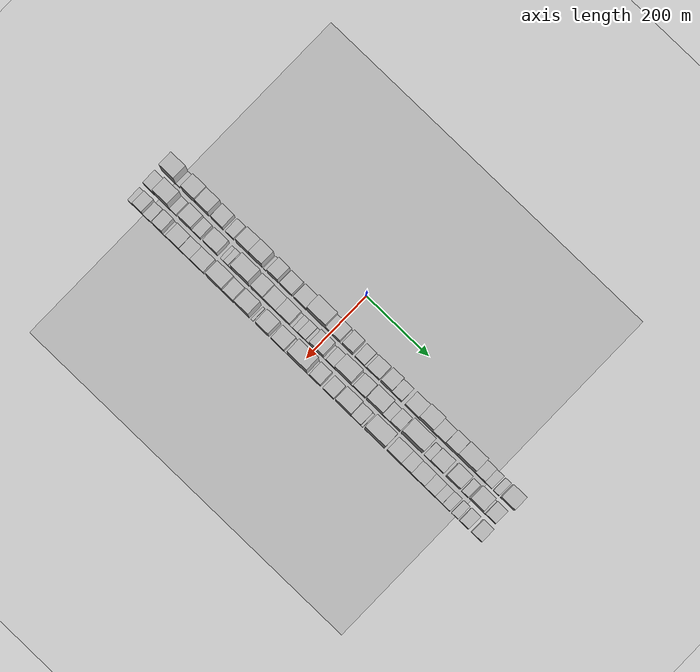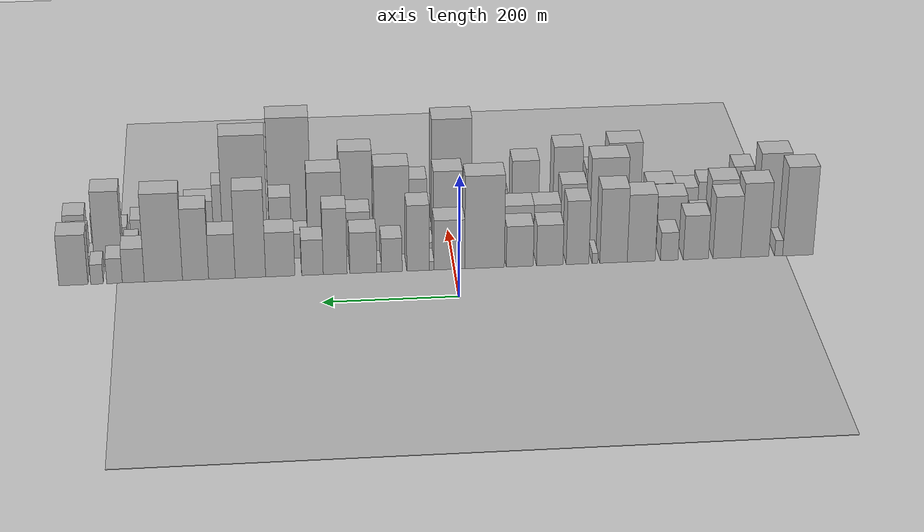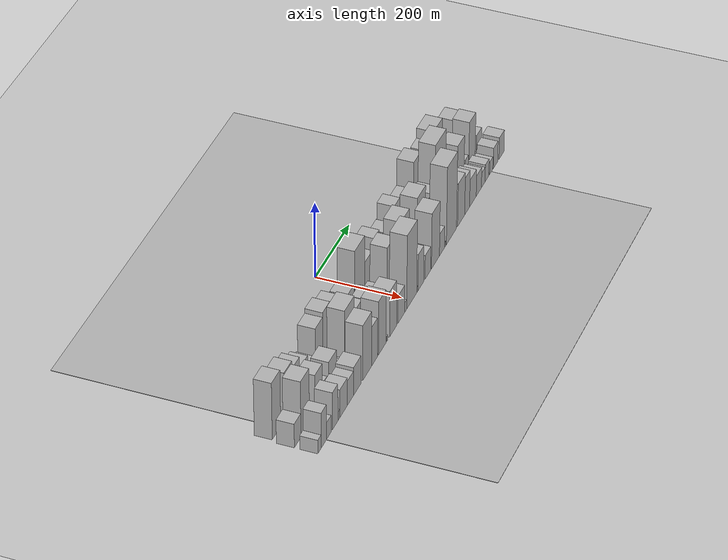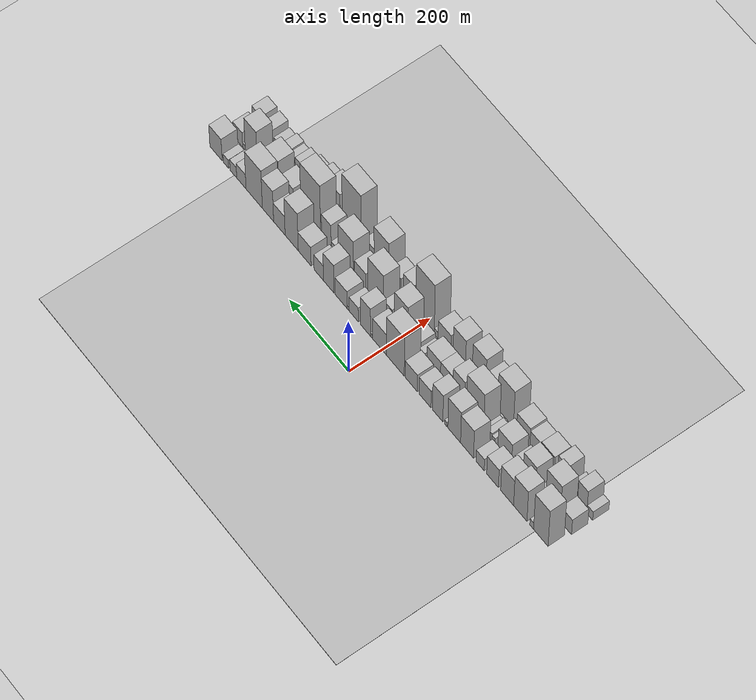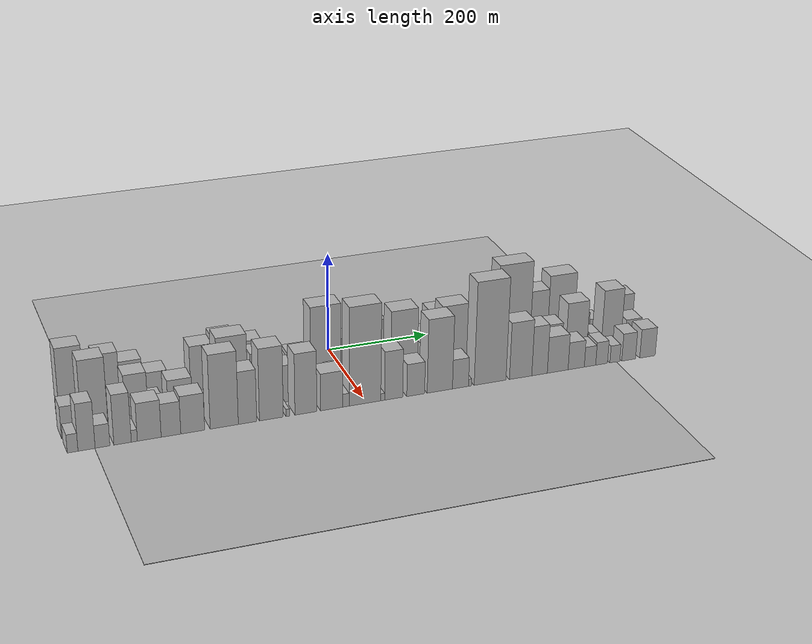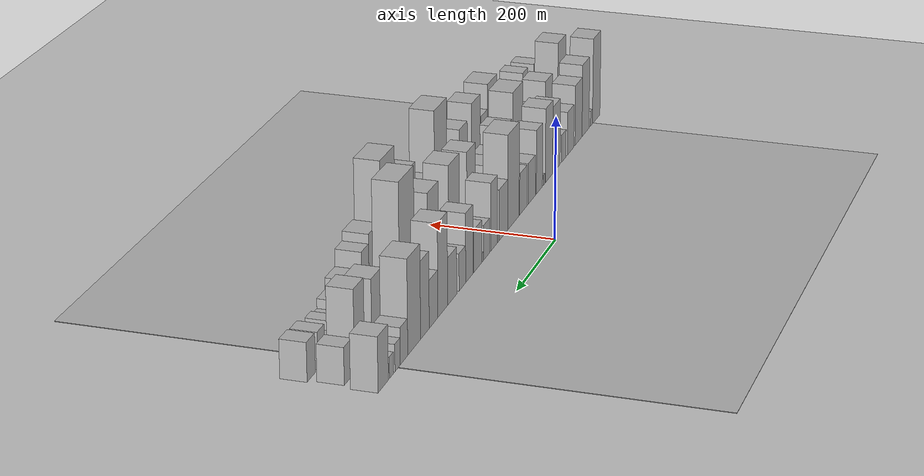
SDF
<?xml version="1.0" encoding="utf-8"?>

<sdf version="1.6">

   <world name="default">

      <gui fullscreen="0">

         <camera name="user_camera">

            <pose>-15 0 4.57585 0 0 0</pose>

            <view_controller>orbit</view_controller>

         </camera>

      </gui>

      <scene>

         <sky>

           <clouds>

             <speed>12</speed>

           </clouds>

         </sky>

         <ambient>0.4 0.4 0.4 1</ambient>

         <background>0.7 0.7 0.7 1</background>

         <shadows>1</shadows>

      </scene>

      <gravity>0 0 -9.8066</gravity>

      <magnetic_field>6e-06 2.3e-05 -4.2e-05</magnetic_field>

      <physics default="0" name="default_physics" type="ode">

         <ode>

            <solver>

               <type>quick</type>

               <iters>10</iters>

               <sor>1.0</sor>

               <use_dynamic_moi_rescaling>0</use_dynamic_moi_rescaling>

            </solver>

            <constraints>

               <cfm>0</cfm>

               <erp>0.2</erp>

               <contact_max_correcting_vel>100</contact_max_correcting_vel>

               <contact_surface_layer>0.001</contact_surface_layer>

            </constraints>

         </ode>

         <max_step_size>0.004</max_step_size>

         <real_time_factor>1</real_time_factor>

         <real_time_update_rate>250</real_time_update_rate>

      </physics>

      <light name="sun" type="directional">

         <cast_shadows>1</cast_shadows>

         <pose>0 0 10 0 0 0</pose>

         <diffuse>0.8 0.8 0.8 1</diffuse>

         <specular>0.2 0.2 0.2 1</specular>

         <attenuation>

            <range>1000</range>

            <constant>0.9</constant>

            <linear>0.01</linear>

            <quadratic>0.001</quadratic>

         </attenuation>

         <direction>-0.5 0.1 -0.9</direction>

      </light>

      <include>

         <name>ground_plane_1</name>

         <uri>model://HANNAS_ground_plane</uri>

         <pose>0 0 0  0 0 0</pose>

      </include>

      <include>

         <name>ground_plane_2</name>

         <uri>model://HANNAS_ground_plane</uri>

         <pose>100 0 0  0 0 0</pose>

      </include>

      <model name="building_1">

         <static>1</static>

         <pose frame="">100.0000 -517.8129 0 0.000000 0.000000 0.000000</pose>

         <link name="link">

            <pose frame="">0 0 75.00 0 0 0</pose>

            <collision name="collision">

               <geometry>

                  <box>

                     <size>40.0000 46.3742 150.0000</size>

                  </box>

               </geometry>

               <max_contacts>10</max_contacts>

               <surface>

                  <contact>

                     <ode/>

                  </contact>

                  <bounce/>

                  <friction>

                     <torsional>

                        <ode/>

                     </torsional>

                     <ode/>

                  </friction>

               </surface>

            </collision>

            <visual name="visual">

               <cast_shadows>0</cast_shadows>

               <geometry>

                  <box>

                     <size>40.0000 46.3742 150.0000</size>

                  </box>

               </geometry>

               <material>

                  <script>

                     <uri>model://HANNAS_wall/materials/scripts</uri>

                     <uri>model://HANNAS_wall/materials/textures</uri>

                     <name>vrc/HANNAS_wall</name>

                  </script>

               </material>

            </visual>

            <self_collide>0</self_collide>

            <enable_wind>0</enable_wind>

            <kinematic>0</kinematic>

         </link>

      </model>

      <model name="building_2">

         <static>1</static>

         <pose frame="">100.0000 -488.5571 0 0.000000 0.000000 0.000000</pose>

         <link name="link">

            <pose frame="">0 0 13.50 0 0 0</pose>

            <collision name="collision">

               <geometry>

                  <box>

                     <size>40.0000 12.1373 27.0000</size>

                  </box>

               </geometry>

               <max_contacts>10</max_contacts>

               <surface>

                  <contact>

                     <ode/>

                  </contact>

                  <bounce/>

                  <friction>

                     <torsional>

                        <ode/>

                     </torsional>

                     <ode/>

                  </friction>

               </surface>

            </collision>

            <visual name="visual">

               <cast_shadows>0</cast_shadows>

               <geometry>

                  <box>

                     <size>40.0000 12.1373 27.0000</size>

                  </box>

               </geometry>

               <material>

                  <script>

                     <uri>model://HANNAS_wall/materials/scripts</uri>

                     <uri>model://HANNAS_wall/materials/textures</uri>

                     <name>vrc/HANNAS_wall</name>

                  </script>

               </material>

            </visual>

            <self_collide>0</self_collide>

            <enable_wind>0</enable_wind>

            <kinematic>0</kinematic>

         </link>

      </model>

      <model name="building_3">

         <static>1</static>

         <pose frame="">100.0000 -452.1296 0 0.000000 0.000000 0.000000</pose>

         <link name="link">

            <pose frame="">0 0 63.00 0 0 0</pose>

            <collision name="collision">

               <geometry>

                  <box>

                     <size>40.0000 42.7177 126.0000</size>

                  </box>

               </geometry>

               <max_contacts>10</max_contacts>

               <surface>

                  <contact>

                     <ode/>

                  </contact>

                  <bounce/>

                  <friction>

                     <torsional>

                        <ode/>

                     </torsional>

                     <ode/>

                  </friction>

               </surface>

            </collision>

            <visual name="visual">

               <cast_shadows>0</cast_shadows>

               <geometry>

                  <box>

                     <size>40.0000 42.7177 126.0000</size>

                  </box>

               </geometry>

               <material>

                  <script>

                     <uri>model://HANNAS_wall/materials/scripts</uri>

                     <uri>model://HANNAS_wall/materials/textures</uri>

                     <name>vrc/HANNAS_wall</name>

                  </script>

               </material>

            </visual>

            <self_collide>0</self_collide>

            <enable_wind>0</enable_wind>

            <kinematic>0</kinematic>

         </link>

      </model>

      <model name="building_4">

         <static>1</static>

         <pose frame="">100.0000 -409.7963 0 0.000000 0.000000 0.000000</pose>

         <link name="link">

            <pose frame="">0 0 52.50 0 0 0</pose>

            <collision name="collision">

               <geometry>

                  <box>

                     <size>40.0000 41.9489 105.0000</size>

                  </box>

               </geometry>

               <max_contacts>10</max_contacts>

               <surface>

                  <contact>

                     <ode/>

                  </contact>

                  <bounce/>

                  <friction>

                     <torsional>

                        <ode/>

                     </torsional>

                     <ode/>

                  </friction>

               </surface>

            </collision>

            <visual name="visual">

               <cast_shadows>0</cast_shadows>

               <geometry>

                  <box>

                     <size>40.0000 41.9489 105.0000</size>

                  </box>

               </geometry>

               <material>

                  <script>

                     <uri>model://HANNAS_wall/materials/scripts</uri>

                     <uri>model://HANNAS_wall/materials/textures</uri>

                     <name>vrc/HANNAS_wall</name>

                  </script>

               </material>

            </visual>

            <self_collide>0</self_collide>

            <enable_wind>0</enable_wind>

            <kinematic>0</kinematic>

         </link>

      </model>

      <model name="building_5">

         <static>1</static>

         <pose frame="">100.0000 -362.7776 0 0.000000 0.000000 0.000000</pose>

         <link name="link">

            <pose frame="">0 0 37.50 0 0 0</pose>

            <collision name="collision">

               <geometry>

                  <box>

                     <size>40.0000 38.0886 75.0000</size>

                  </box>

               </geometry>

               <max_contacts>10</max_contacts>

               <surface>

                  <contact>

                     <ode/>

                  </contact>

                  <bounce/>

                  <friction>

                     <torsional>

                        <ode/>

                     </torsional>

                     <ode/>

                  </friction>

               </surface>

            </collision>

            <visual name="visual">

               <cast_shadows>0</cast_shadows>

               <geometry>

                  <box>

                     <size>40.0000 38.0886 75.0000</size>

                  </box>

               </geometry>

               <material>

                  <script>

                     <uri>model://HANNAS_wall/materials/scripts</uri>

                     <uri>model://HANNAS_wall/materials/textures</uri>

                     <name>vrc/HANNAS_wall</name>

                  </script>

               </material>

            </visual>

            <self_collide>0</self_collide>

            <enable_wind>0</enable_wind>

            <kinematic>0</kinematic>

         </link>

      </model>

      <model name="building_6">

         <static>1</static>

         <pose frame="">100.0000 -322.4635 0 0.000000 0.000000 0.000000</pose>

         <link name="link">

            <pose frame="">0 0 24.00 0 0 0</pose>

            <collision name="collision">

               <geometry>

                  <box>

                     <size>40.0000 26.5395 48.0000</size>

                  </box>

               </geometry>

               <max_contacts>10</max_contacts>

               <surface>

                  <contact>

                     <ode/>

                  </contact>

                  <bounce/>

                  <friction>

                     <torsional>

                        <ode/>

                     </torsional>

                     <ode/>

                  </friction>

               </surface>

            </collision>

            <visual name="visual">

               <cast_shadows>0</cast_shadows>

               <geometry>

                  <box>

                     <size>40.0000 26.5395 48.0000</size>

                  </box>

               </geometry>

               <material>

                  <script>

                     <uri>model://HANNAS_wall/materials/scripts</uri>

                     <uri>model://HANNAS_wall/materials/textures</uri>

                     <name>vrc/HANNAS_wall</name>

                  </script>

               </material>

            </visual>

            <self_collide>0</self_collide>

            <enable_wind>0</enable_wind>

            <kinematic>0</kinematic>

         </link>

      </model>

      <model name="building_7">

         <static>1</static>

         <pose frame="">100.0000 -280.0874 0 0.000000 0.000000 0.000000</pose>

         <link name="link">

            <pose frame="">0 0 57.00 0 0 0</pose>

            <collision name="collision">

               <geometry>

                  <box>

                     <size>40.0000 42.2128 114.0000</size>

                  </box>

               </geometry>

               <max_contacts>10</max_contacts>

               <surface>

                  <contact>

                     <ode/>

                  </contact>

                  <bounce/>

                  <friction>

                     <torsional>

                        <ode/>

                     </torsional>

                     <ode/>

                  </friction>

               </surface>

            </collision>

            <visual name="visual">

               <cast_shadows>0</cast_shadows>

               <geometry>

                  <box>

                     <size>40.0000 42.2128 114.0000</size>

                  </box>

               </geometry>

               <material>

                  <script>

                     <uri>model://HANNAS_wall/materials/scripts</uri>

                     <uri>model://HANNAS_wall/materials/textures</uri>

                     <name>vrc/HANNAS_wall</name>

                  </script>

               </material>

            </visual>

            <self_collide>0</self_collide>

            <enable_wind>0</enable_wind>

            <kinematic>0</kinematic>

         </link>

      </model>

      <model name="building_8">

         <static>1</static>

         <pose frame="">100.0000 -238.3081 0 0.000000 0.000000 0.000000</pose>

         <link name="link">

            <pose frame="">0 0 63.00 0 0 0</pose>

            <collision name="collision">

               <geometry>

                  <box>

                     <size>40.0000 41.3457 126.0000</size>

                  </box>

               </geometry>

               <max_contacts>10</max_contacts>

               <surface>

                  <contact>

                     <ode/>

                  </contact>

                  <bounce/>

                  <friction>

                     <torsional>

                        <ode/>

                     </torsional>

                     <ode/>

                  </friction>

               </surface>

            </collision>

            <visual name="visual">

               <cast_shadows>0</cast_shadows>

               <geometry>

                  <box>

                     <size>40.0000 41.3457 126.0000</size>

                  </box>

               </geometry>

               <material>

                  <script>

                     <uri>model://HANNAS_wall/materials/scripts</uri>

                     <uri>model://HANNAS_wall/materials/textures</uri>

                     <name>vrc/HANNAS_wall</name>

                  </script>

               </material>

            </visual>

            <self_collide>0</self_collide>

            <enable_wind>0</enable_wind>

            <kinematic>0</kinematic>

         </link>

      </model>

      <model name="building_9">

         <static>1</static>

         <pose frame="">100.0000 -210.3864 0 0.000000 0.000000 0.000000</pose>

         <link name="link">

            <pose frame="">0 0 9.00 0 0 0</pose>

            <collision name="collision">

               <geometry>

                  <box>

                     <size>40.0000 8.4978 18.0000</size>

                  </box>

               </geometry>

               <max_contacts>10</max_contacts>

               <surface>

                  <contact>

                     <ode/>

                  </contact>

                  <bounce/>

                  <friction>

                     <torsional>

                        <ode/>

                     </torsional>

                     <ode/>

                  </friction>

               </surface>

            </collision>

            <visual name="visual">

               <cast_shadows>0</cast_shadows>

               <geometry>

                  <box>

                     <size>40.0000 8.4978 18.0000</size>

                  </box>

               </geometry>

               <material>

                  <script>

                     <uri>model://HANNAS_wall/materials/scripts</uri>

                     <uri>model://HANNAS_wall/materials/textures</uri>

                     <name>vrc/HANNAS_wall</name>

                  </script>

               </material>

            </visual>

            <self_collide>0</self_collide>

            <enable_wind>0</enable_wind>

            <kinematic>0</kinematic>

         </link>

      </model>

      <model name="building_10">

         <static>1</static>

         <pose frame="">100.0000 -184.0744 0 0.000000 0.000000 0.000000</pose>

         <link name="link">

            <pose frame="">0 0 54.00 0 0 0</pose>

            <collision name="collision">

               <geometry>

                  <box>

                     <size>40.0000 34.1261 108.0000</size>

                  </box>

               </geometry>

               <max_contacts>10</max_contacts>

               <surface>

                  <contact>

                     <ode/>

                  </contact>

                  <bounce/>

                  <friction>

                     <torsional>

                        <ode/>

                     </torsional>

                     <ode/>

                  </friction>

               </surface>

            </collision>

            <visual name="visual">

               <cast_shadows>0</cast_shadows>

               <geometry>

                  <box>

                     <size>40.0000 34.1261 108.0000</size>

                  </box>

               </geometry>

               <material>

                  <script>

                     <uri>model://HANNAS_wall/materials/scripts</uri>

                     <uri>model://HANNAS_wall/materials/textures</uri>

                     <name>vrc/HANNAS_wall</name>

                  </script>

               </material>

            </visual>

            <self_collide>0</self_collide>

            <enable_wind>0</enable_wind>

            <kinematic>0</kinematic>

         </link>

      </model>

      <model name="building_11">

         <static>1</static>

         <pose frame="">100.0000 -142.2637 0 0.000000 0.000000 0.000000</pose>

         <link name="link">

            <pose frame="">0 0 34.50 0 0 0</pose>

            <collision name="collision">

               <geometry>

                  <box>

                     <size>40.0000 39.4953 69.0000</size>

                  </box>

               </geometry>

               <max_contacts>10</max_contacts>

               <surface>

                  <contact>

                     <ode/>

                  </contact>

                  <bounce/>

                  <friction>

                     <torsional>

                        <ode/>

                     </torsional>

                     <ode/>

                  </friction>

               </surface>

            </collision>

            <visual name="visual">

               <cast_shadows>0</cast_shadows>

               <geometry>

                  <box>

                     <size>40.0000 39.4953 69.0000</size>

                  </box>

               </geometry>

               <material>

                  <script>

                     <uri>model://HANNAS_wall/materials/scripts</uri>

                     <uri>model://HANNAS_wall/materials/textures</uri>

                     <name>vrc/HANNAS_wall</name>

                  </script>

               </material>

            </visual>

            <self_collide>0</self_collide>

            <enable_wind>0</enable_wind>

            <kinematic>0</kinematic>

         </link>

      </model>

      <model name="building_12">

         <static>1</static>

         <pose frame="">100.0000 -97.3337 0 0.000000 0.000000 0.000000</pose>

         <link name="link">

            <pose frame="">0 0 34.50 0 0 0</pose>

            <collision name="collision">

               <geometry>

                  <box>

                     <size>40.0000 40.3648 69.0000</size>

                  </box>

               </geometry>

               <max_contacts>10</max_contacts>

               <surface>

                  <contact>

                     <ode/>

                  </contact>

                  <bounce/>

                  <friction>

                     <torsional>

                        <ode/>

                     </torsional>

                     <ode/>

                  </friction>

               </surface>

            </collision>

            <visual name="visual">

               <cast_shadows>0</cast_shadows>

               <geometry>

                  <box>

                     <size>40.0000 40.3648 69.0000</size>

                  </box>

               </geometry>

               <material>

                  <script>

                     <uri>model://HANNAS_wall/materials/scripts</uri>

                     <uri>model://HANNAS_wall/materials/textures</uri>

                     <name>vrc/HANNAS_wall</name>

                  </script>

               </material>

            </visual>

            <self_collide>0</self_collide>

            <enable_wind>0</enable_wind>

            <kinematic>0</kinematic>

         </link>

      </model>

      <model name="building_13">

         <static>1</static>

         <pose frame="">100.0000 -44.5893 0 0.000000 0.000000 0.000000</pose>

         <link name="link">

            <pose frame="">0 0 78.00 0 0 0</pose>

            <collision name="collision">

               <geometry>

                  <box>

                     <size>40.0000 59.1241 156.0000</size>

                  </box>

               </geometry>

               <max_contacts>10</max_contacts>

               <surface>

                  <contact>

                     <ode/>

                  </contact>

                  <bounce/>

                  <friction>

                     <torsional>

                        <ode/>

                     </torsional>

                     <ode/>

                  </friction>

               </surface>

            </collision>

            <visual name="visual">

               <cast_shadows>0</cast_shadows>

               <geometry>

                  <box>

                     <size>40.0000 59.1241 156.0000</size>

                  </box>

               </geometry>

               <material>

                  <script>

                     <uri>model://HANNAS_wall/materials/scripts</uri>

                     <uri>model://HANNAS_wall/materials/textures</uri>

                     <name>vrc/HANNAS_wall</name>

                  </script>

               </material>

            </visual>

            <self_collide>0</self_collide>

            <enable_wind>0</enable_wind>

            <kinematic>0</kinematic>

         </link>

      </model>

      <model name="building_14">

         <static>1</static>

         <pose frame="">100.0000 7.8400 0 0.000000 0.000000 0.000000</pose>

         <link name="link">

            <pose frame="">0 0 42.00 0 0 0</pose>

            <collision name="collision">

               <geometry>

                  <box>

                     <size>40.0000 45.7345 84.0000</size>

                  </box>

               </geometry>

               <max_contacts>10</max_contacts>

               <surface>

                  <contact>

                     <ode/>

                  </contact>

                  <bounce/>

                  <friction>

                     <torsional>

                        <ode/>

                     </torsional>

                     <ode/>

                  </friction>

               </surface>

            </collision>

            <visual name="visual">

               <cast_shadows>0</cast_shadows>

               <geometry>

                  <box>

                     <size>40.0000 45.7345 84.0000</size>

                  </box>

               </geometry>

               <material>

                  <script>

                     <uri>model://HANNAS_wall/materials/scripts</uri>

                     <uri>model://HANNAS_wall/materials/textures</uri>

                     <name>vrc/HANNAS_wall</name>

                  </script>

               </material>

            </visual>

            <self_collide>0</self_collide>

            <enable_wind>0</enable_wind>

            <kinematic>0</kinematic>

         </link>

      </model>

      <model name="building_15">

         <static>1</static>

         <pose frame="">100.0000 34.3430 0 0.000000 0.000000 0.000000</pose>

         <link name="link">

            <pose frame="">0 0 7.50 0 0 0</pose>

            <collision name="collision">

               <geometry>

                  <box>

                     <size>40.0000 7.2717 15.0000</size>

                  </box>

               </geometry>

               <max_contacts>10</max_contacts>

               <surface>

                  <contact>

                     <ode/>

                  </contact>

                  <bounce/>

                  <friction>

                     <torsional>

                        <ode/>

                     </torsional>

                     <ode/>

                  </friction>

               </surface>

            </collision>

            <visual name="visual">

               <cast_shadows>0</cast_shadows>

               <geometry>

                  <box>

                     <size>40.0000 7.2717 15.0000</size>

                  </box>

               </geometry>

               <material>

                  <script>

                     <uri>model://HANNAS_wall/materials/scripts</uri>

                     <uri>model://HANNAS_wall/materials/textures</uri>

                     <name>vrc/HANNAS_wall</name>

                  </script>

               </material>

            </visual>

            <self_collide>0</self_collide>

            <enable_wind>0</enable_wind>

            <kinematic>0</kinematic>

         </link>

      </model>

      <model name="building_16">

         <static>1</static>

         <pose frame="">100.0000 54.7436 0 0.000000 0.000000 0.000000</pose>

         <link name="link">

            <pose frame="">0 0 55.50 0 0 0</pose>

            <collision name="collision">

               <geometry>

                  <box>

                     <size>40.0000 33.5295 111.0000</size>

                  </box>

               </geometry>

               <max_contacts>10</max_contacts>

               <surface>

                  <contact>

                     <ode/>

                  </contact>

                  <bounce/>

                  <friction>

                     <torsional>

                        <ode/>

                     </torsional>

                     <ode/>

                  </friction>

               </surface>

            </collision>

            <visual name="visual">

               <cast_shadows>0</cast_shadows>

               <geometry>

                  <box>

                     <size>40.0000 33.5295 111.0000</size>

                  </box>

               </geometry>

               <material>

                  <script>

                     <uri>model://HANNAS_wall/materials/scripts</uri>

                     <uri>model://HANNAS_wall/materials/textures</uri>

                     <name>vrc/HANNAS_wall</name>

                  </script>

               </material>

            </visual>

            <self_collide>0</self_collide>

            <enable_wind>0</enable_wind>

            <kinematic>0</kinematic>

         </link>

      </model>

      <model name="building_17">

         <static>1</static>

         <pose frame="">100.0000 93.9533 0 0.000000 0.000000 0.000000</pose>

         <link name="link">

            <pose frame="">0 0 28.50 0 0 0</pose>

            <collision name="collision">

               <geometry>

                  <box>

                     <size>40.0000 30.8900 57.0000</size>

                  </box>

               </geometry>

               <max_contacts>10</max_contacts>

               <surface>

                  <contact>

                     <ode/>

                  </contact>

                  <bounce/>

                  <friction>

                     <torsional>

                        <ode/>

                     </torsional>

                     <ode/>

                  </friction>

               </surface>

            </collision>

            <visual name="visual">

               <cast_shadows>0</cast_shadows>

               <geometry>

                  <box>

                     <size>40.0000 30.8900 57.0000</size>

                  </box>

               </geometry>

               <material>

                  <script>

                     <uri>model://HANNAS_wall/materials/scripts</uri>

                     <uri>model://HANNAS_wall/materials/textures</uri>

                     <name>vrc/HANNAS_wall</name>

                  </script>

               </material>

            </visual>

            <self_collide>0</self_collide>

            <enable_wind>0</enable_wind>

            <kinematic>0</kinematic>

         </link>

      </model>

      <model name="building_18">

         <static>1</static>

         <pose frame="">100.0000 112.8264 0 0.000000 0.000000 0.000000</pose>

         <link name="link">

            <pose frame="">0 0 7.50 0 0 0</pose>

            <collision name="collision">

               <geometry>

                  <box>

                     <size>40.0000 6.8562 15.0000</size>

                  </box>

               </geometry>

               <max_contacts>10</max_contacts>

               <surface>

                  <contact>

                     <ode/>

                  </contact>

                  <bounce/>

                  <friction>

                     <torsional>

                        <ode/>

                     </torsional>

                     <ode/>

                  </friction>

               </surface>

            </collision>

            <visual name="visual">

               <cast_shadows>0</cast_shadows>

               <geometry>

                  <box>

                     <size>40.0000 6.8562 15.0000</size>

                  </box>

               </geometry>

               <material>

                  <script>

                     <uri>model://HANNAS_wall/materials/scripts</uri>

                     <uri>model://HANNAS_wall/materials/textures</uri>

                     <name>vrc/HANNAS_wall</name>

                  </script>

               </material>

            </visual>

            <self_collide>0</self_collide>

            <enable_wind>0</enable_wind>

            <kinematic>0</kinematic>

         </link>

      </model>

      <model name="building_19">

         <static>1</static>

         <pose frame="">100.0000 136.2971 0 0.000000 0.000000 0.000000</pose>

         <link name="link">

            <pose frame="">0 0 34.50 0 0 0</pose>

            <collision name="collision">

               <geometry>

                  <box>

                     <size>40.0000 40.0853 69.0000</size>

                  </box>

               </geometry>

               <max_contacts>10</max_contacts>

               <surface>

                  <contact>

                     <ode/>

                  </contact>

                  <bounce/>

                  <friction>

                     <torsional>

                        <ode/>

                     </torsional>

                     <ode/>

                  </friction>

               </surface>

            </collision>

            <visual name="visual">

               <cast_shadows>0</cast_shadows>

               <geometry>

                  <box>

                     <size>40.0000 40.0853 69.0000</size>

                  </box>

               </geometry>

               <material>

                  <script>

                     <uri>model://HANNAS_wall/materials/scripts</uri>

                     <uri>model://HANNAS_wall/materials/textures</uri>

                     <name>vrc/HANNAS_wall</name>

                  </script>

               </material>

            </visual>

            <self_collide>0</self_collide>

            <enable_wind>0</enable_wind>

            <kinematic>0</kinematic>

         </link>

      </model>

      <model name="building_20">

         <static>1</static>

         <pose frame="">100.0000 178.0922 0 0.000000 0.000000 0.000000</pose>

         <link name="link">

            <pose frame="">0 0 55.50 0 0 0</pose>

            <collision name="collision">

               <geometry>

                  <box>

                     <size>40.0000 35.5049 111.0000</size>

                  </box>

               </geometry>

               <max_contacts>10</max_contacts>

               <surface>

                  <contact>

                     <ode/>

                  </contact>

                  <bounce/>

                  <friction>

                     <torsional>

                        <ode/>

                     </torsional>

                     <ode/>

                  </friction>

               </surface>

            </collision>

            <visual name="visual">

               <cast_shadows>0</cast_shadows>

               <geometry>

                  <box>

                     <size>40.0000 35.5049 111.0000</size>

                  </box>

               </geometry>

               <material>

                  <script>

                     <uri>model://HANNAS_wall/materials/scripts</uri>

                     <uri>model://HANNAS_wall/materials/textures</uri>

                     <name>vrc/HANNAS_wall</name>

                  </script>

               </material>

            </visual>

            <self_collide>0</self_collide>

            <enable_wind>0</enable_wind>

            <kinematic>0</kinematic>

         </link>

      </model>

      <model name="building_21">

         <static>1</static>

         <pose frame="">100.0000 211.8071 0 0.000000 0.000000 0.000000</pose>

         <link name="link">

            <pose frame="">0 0 30.00 0 0 0</pose>

            <collision name="collision">

               <geometry>

                  <box>

                     <size>40.0000 31.9250 60.0000</size>

                  </box>

               </geometry>

               <max_contacts>10</max_contacts>

               <surface>

                  <contact>

                     <ode/>

                  </contact>

                  <bounce/>

                  <friction>

                     <torsional>

                        <ode/>

                     </torsional>

                     <ode/>

                  </friction>

               </surface>

            </collision>

            <visual name="visual">

               <cast_shadows>0</cast_shadows>

               <geometry>

                  <box>

                     <size>40.0000 31.9250 60.0000</size>

                  </box>

               </geometry>

               <material>

                  <script>

                     <uri>model://HANNAS_wall/materials/scripts</uri>

                     <uri>model://HANNAS_wall/materials/textures</uri>

                     <name>vrc/HANNAS_wall</name>

                  </script>

               </material>

            </visual>

            <self_collide>0</self_collide>

            <enable_wind>0</enable_wind>

            <kinematic>0</kinematic>

         </link>

      </model>

      <model name="building_22">

         <static>1</static>

         <pose frame="">100.0000 259.4445 0 0.000000 0.000000 0.000000</pose>

         <link name="link">

            <pose frame="">0 0 37.50 0 0 0</pose>

            <collision name="collision">

               <geometry>

                  <box>

                     <size>40.0000 43.3497 75.0000</size>

                  </box>

               </geometry>

               <max_contacts>10</max_contacts>

               <surface>

                  <contact>

                     <ode/>

                  </contact>

                  <bounce/>

                  <friction>

                     <torsional>

                        <ode/>

                     </torsional>

                     <ode/>

                  </friction>

               </surface>

            </collision>

            <visual name="visual">

               <cast_shadows>0</cast_shadows>

               <geometry>

                  <box>

                     <size>40.0000 43.3497 75.0000</size>

                  </box>

               </geometry>

               <material>

                  <script>

                     <uri>model://HANNAS_wall/materials/scripts</uri>

                     <uri>model://HANNAS_wall/materials/textures</uri>

                     <name>vrc/HANNAS_wall</name>

                  </script>

               </material>

            </visual>

            <self_collide>0</self_collide>

            <enable_wind>0</enable_wind>

            <kinematic>0</kinematic>

         </link>

      </model>

      <model name="building_23">

         <static>1</static>

         <pose frame="">100.0000 303.5322 0 0.000000 0.000000 0.000000</pose>

         <link name="link">

            <pose frame="">0 0 73.50 0 0 0</pose>

            <collision name="collision">

               <geometry>

                  <box>

                     <size>40.0000 44.8257 147.0000</size>

                  </box>

               </geometry>

               <max_contacts>10</max_contacts>

               <surface>

                  <contact>

                     <ode/>

                  </contact>

                  <bounce/>

                  <friction>

                     <torsional>

                        <ode/>

                     </torsional>

                     <ode/>

                  </friction>

               </surface>

            </collision>

            <visual name="visual">

               <cast_shadows>0</cast_shadows>

               <geometry>

                  <box>

                     <size>40.0000 44.8257 147.0000</size>

                  </box>

               </geometry>

               <material>

                  <script>

                     <uri>model://HANNAS_wall/materials/scripts</uri>

                     <uri>model://HANNAS_wall/materials/textures</uri>

                     <name>vrc/HANNAS_wall</name>

                  </script>

               </material>

            </visual>

            <self_collide>0</self_collide>

            <enable_wind>0</enable_wind>

            <kinematic>0</kinematic>

         </link>

      </model>

      <model name="building_24">

         <static>1</static>

         <pose frame="">100.0000 345.5613 0 0.000000 0.000000 0.000000</pose>

         <link name="link">

            <pose frame="">0 0 37.50 0 0 0</pose>

            <collision name="collision">

               <geometry>

                  <box>

                     <size>40.0000 39.2325 75.0000</size>

                  </box>

               </geometry>

               <max_contacts>10</max_contacts>

               <surface>

                  <contact>

                     <ode/>

                  </contact>

                  <bounce/>

                  <friction>

                     <torsional>

                        <ode/>

                     </torsional>

                     <ode/>

                  </friction>

               </surface>

            </collision>

            <visual name="visual">

               <cast_shadows>0</cast_shadows>

               <geometry>

                  <box>

                     <size>40.0000 39.2325 75.0000</size>

                  </box>

               </geometry>

               <material>

                  <script>

                     <uri>model://HANNAS_wall/materials/scripts</uri>

                     <uri>model://HANNAS_wall/materials/textures</uri>

                     <name>vrc/HANNAS_wall</name>

                  </script>

               </material>

            </visual>

            <self_collide>0</self_collide>

            <enable_wind>0</enable_wind>

            <kinematic>0</kinematic>

         </link>

      </model>

      <model name="building_25">

         <static>1</static>

         <pose frame="">100.0000 384.4321 0 0.000000 0.000000 0.000000</pose>

         <link name="link">

            <pose frame="">0 0 60.00 0 0 0</pose>

            <collision name="collision">

               <geometry>

                  <box>

                     <size>40.0000 38.5091 120.0000</size>

                  </box>

               </geometry>

               <max_contacts>10</max_contacts>

               <surface>

                  <contact>

                     <ode/>

                  </contact>

                  <bounce/>

                  <friction>

                     <torsional>

                        <ode/>

                     </torsional>

                     <ode/>

                  </friction>

               </surface>

            </collision>

            <visual name="visual">

               <cast_shadows>0</cast_shadows>

               <geometry>

                  <box>

                     <size>40.0000 38.5091 120.0000</size>

                  </box>

               </geometry>

               <material>

                  <script>

                     <uri>model://HANNAS_wall/materials/scripts</uri>

                     <uri>model://HANNAS_wall/materials/textures</uri>

                     <name>vrc/HANNAS_wall</name>

                  </script>

               </material>

            </visual>

            <self_collide>0</self_collide>

            <enable_wind>0</enable_wind>

            <kinematic>0</kinematic>

         </link>

      </model>

      <model name="building_26">

         <static>1</static>

         <pose frame="">100.0000 431.7537 0 0.000000 0.000000 0.000000</pose>

         <link name="link">

            <pose frame="">0 0 73.50 0 0 0</pose>

            <collision name="collision">

               <geometry>

                  <box>

                     <size>40.0000 56.1342 147.0000</size>

                  </box>

               </geometry>

               <max_contacts>10</max_contacts>

               <surface>

                  <contact>

                     <ode/>

                  </contact>

                  <bounce/>

                  <friction>

                     <torsional>

                        <ode/>

                     </torsional>

                     <ode/>

                  </friction>

               </surface>

            </collision>

            <visual name="visual">

               <cast_shadows>0</cast_shadows>

               <geometry>

                  <box>

                     <size>40.0000 56.1342 147.0000</size>

                  </box>

               </geometry>

               <material>

                  <script>

                     <uri>model://HANNAS_wall/materials/scripts</uri>

                     <uri>model://HANNAS_wall/materials/textures</uri>

                     <name>vrc/HANNAS_wall</name>

                  </script>

               </material>

            </visual>

            <self_collide>0</self_collide>

            <enable_wind>0</enable_wind>

            <kinematic>0</kinematic>

         </link>

      </model>

      <model name="building_27">

         <static>1</static>

         <pose frame="">100.0000 475.9596 0 0.000000 0.000000 0.000000</pose>

         <link name="link">

            <pose frame="">0 0 28.50 0 0 0</pose>

            <collision name="collision">

               <geometry>

                  <box>

                     <size>40.0000 32.2775 57.0000</size>

                  </box>

               </geometry>

               <max_contacts>10</max_contacts>

               <surface>

                  <contact>

                     <ode/>

                  </contact>

                  <bounce/>

                  <friction>

                     <torsional>

                        <ode/>

                     </torsional>

                     <ode/>

                  </friction>

               </surface>

            </collision>

            <visual name="visual">

               <cast_shadows>0</cast_shadows>

               <geometry>

                  <box>

                     <size>40.0000 32.2775 57.0000</size>

                  </box>

               </geometry>

               <material>

                  <script>

                     <uri>model://HANNAS_wall/materials/scripts</uri>

                     <uri>model://HANNAS_wall/materials/textures</uri>

                     <name>vrc/HANNAS_wall</name>

                  </script>

               </material>

            </visual>

            <self_collide>0</self_collide>

            <enable_wind>0</enable_wind>

            <kinematic>0</kinematic>

         </link>

      </model>

      <model name="building_28">

         <static>1</static>

         <pose frame="">100.0000 503.5935 0 0.000000 0.000000 0.000000</pose>

         <link name="link">

            <pose frame="">0 0 21.00 0 0 0</pose>

            <collision name="collision">

               <geometry>

                  <box>

                     <size>40.0000 22.9903 42.0000</size>

                  </box>

               </geometry>

               <max_contacts>10</max_contacts>

               <surface>

                  <contact>

                     <ode/>

                  </contact>

                  <bounce/>

                  <friction>

                     <torsional>

                        <ode/>

                     </torsional>

                     <ode/>

                  </friction>

               </surface>

            </collision>

            <visual name="visual">

               <cast_shadows>0</cast_shadows>

               <geometry>

                  <box>

                     <size>40.0000 22.9903 42.0000</size>

                  </box>

               </geometry>

               <material>

                  <script>

                     <uri>model://HANNAS_wall/materials/scripts</uri>

                     <uri>model://HANNAS_wall/materials/textures</uri>

                     <name>vrc/HANNAS_wall</name>

                  </script>

               </material>

            </visual>

            <self_collide>0</self_collide>

            <enable_wind>0</enable_wind>

            <kinematic>0</kinematic>

         </link>

      </model>

      <model name="building_29">

         <static>1</static>

         <pose frame="">100.0000 529.2571 0 0.000000 0.000000 0.000000</pose>

         <link name="link">

            <pose frame="">0 0 16.50 0 0 0</pose>

            <collision name="collision">

               <geometry>

                  <box>

                     <size>40.0000 18.3371 33.0000</size>

                  </box>

               </geometry>

               <max_contacts>10</max_contacts>

               <surface>

                  <contact>

                     <ode/>

                  </contact>

                  <bounce/>

                  <friction>

                     <torsional>

                        <ode/>

                     </torsional>

                     <ode/>

                  </friction>

               </surface>

            </collision>

            <visual name="visual">

               <cast_shadows>0</cast_shadows>

               <geometry>

                  <box>

                     <size>40.0000 18.3371 33.0000</size>

                  </box>

               </geometry>

               <material>

                  <script>

                     <uri>model://HANNAS_wall/materials/scripts</uri>

                     <uri>model://HANNAS_wall/materials/textures</uri>

                     <name>vrc/HANNAS_wall</name>

                  </script>

               </material>

            </visual>

            <self_collide>0</self_collide>

            <enable_wind>0</enable_wind>

            <kinematic>0</kinematic>

         </link>

      </model>

      <model name="building_30">

         <static>1</static>

         <pose frame="">100.0000 563.7193 0 0.000000 0.000000 0.000000</pose>

         <link name="link">

            <pose frame="">0 0 42.00 0 0 0</pose>

            <collision name="collision">

               <geometry>

                  <box>

                     <size>40.0000 42.5873 84.0000</size>

                  </box>

               </geometry>

               <max_contacts>10</max_contacts>

               <surface>

                  <contact>

                     <ode/>

                  </contact>

                  <bounce/>

                  <friction>

                     <torsional>

                        <ode/>

                     </torsional>

                     <ode/>

                  </friction>

               </surface>

            </collision>

            <visual name="visual">

               <cast_shadows>0</cast_shadows>

               <geometry>

                  <box>

                     <size>40.0000 42.5873 84.0000</size>

                  </box>

               </geometry>

               <material>

                  <script>

                     <uri>model://HANNAS_wall/materials/scripts</uri>

                     <uri>model://HANNAS_wall/materials/textures</uri>

                     <name>vrc/HANNAS_wall</name>

                  </script>

               </material>

            </visual>

            <self_collide>0</self_collide>

            <enable_wind>0</enable_wind>

            <kinematic>0</kinematic>

         </link>

      </model>

      <model name="building_31">

         <static>1</static>

         <pose frame="">152.0000 -529.8359 0 0.000000 0.000000 0.000000</pose>

         <link name="link">

            <pose frame="">0 0 31.50 0 0 0</pose>

            <collision name="collision">

               <geometry>

                  <box>

                     <size>40.0000 36.3281 63.0000</size>

                  </box>

               </geometry>

               <max_contacts>10</max_contacts>

               <surface>

                  <contact>

                     <ode/>

                  </contact>

                  <bounce/>

                  <friction>

                     <torsional>

                        <ode/>

                     </torsional>

                     <ode/>

                  </friction>

               </surface>

            </collision>

            <visual name="visual">

               <cast_shadows>0</cast_shadows>

               <geometry>

                  <box>

                     <size>40.0000 36.3281 63.0000</size>

                  </box>

               </geometry>

               <material>

                  <script>

                     <uri>model://HANNAS_wall/materials/scripts</uri>

                     <uri>model://HANNAS_wall/materials/textures</uri>

                     <name>vrc/HANNAS_wall</name>

                  </script>

               </material>

            </visual>

            <self_collide>0</self_collide>

            <enable_wind>0</enable_wind>

            <kinematic>0</kinematic>

         </link>

      </model>

      <model name="building_32">

         <static>1</static>

         <pose frame="">152.0000 -488.1662 0 0.000000 0.000000 0.000000</pose>

         <link name="link">

            <pose frame="">0 0 73.50 0 0 0</pose>

            <collision name="collision">

               <geometry>

                  <box>

                     <size>40.0000 47.0113 147.0000</size>

                  </box>

               </geometry>

               <max_contacts>10</max_contacts>

               <surface>

                  <contact>

                     <ode/>

                  </contact>

                  <bounce/>

                  <friction>

                     <torsional>

                        <ode/>

                     </torsional>

                     <ode/>

                  </friction>

               </surface>

            </collision>

            <visual name="visual">

               <cast_shadows>0</cast_shadows>

               <geometry>

                  <box>

                     <size>40.0000 47.0113 147.0000</size>

                  </box>

               </geometry>

               <material>

                  <script>

                     <uri>model://HANNAS_wall/materials/scripts</uri>

                     <uri>model://HANNAS_wall/materials/textures</uri>

                     <name>vrc/HANNAS_wall</name>

                  </script>

               </material>

            </visual>

            <self_collide>0</self_collide>

            <enable_wind>0</enable_wind>

            <kinematic>0</kinematic>

         </link>

      </model>

      <model name="building_33">

         <static>1</static>

         <pose frame="">152.0000 -453.7050 0 0.000000 0.000000 0.000000</pose>

         <link name="link">

            <pose frame="">0 0 19.50 0 0 0</pose>

            <collision name="collision">

               <geometry>

                  <box>

                     <size>40.0000 21.9111 39.0000</size>

                  </box>

               </geometry>

               <max_contacts>10</max_contacts>

               <surface>

                  <contact>

                     <ode/>

                  </contact>

                  <bounce/>

                  <friction>

                     <torsional>

                        <ode/>

                     </torsional>

                     <ode/>

                  </friction>

               </surface>

            </collision>

            <visual name="visual">

               <cast_shadows>0</cast_shadows>

               <geometry>

                  <box>

                     <size>40.0000 21.9111 39.0000</size>

                  </box>

               </geometry>

               <material>

                  <script>

                     <uri>model://HANNAS_wall/materials/scripts</uri>

                     <uri>model://HANNAS_wall/materials/textures</uri>

                     <name>vrc/HANNAS_wall</name>

                  </script>

               </material>

            </visual>

            <self_collide>0</self_collide>

            <enable_wind>0</enable_wind>

            <kinematic>0</kinematic>

         </link>

      </model>

      <model name="building_34">

         <static>1</static>

         <pose frame="">152.0000 -413.0105 0 0.000000 0.000000 0.000000</pose>

         <link name="link">

            <pose frame="">0 0 52.50 0 0 0</pose>

            <collision name="collision">

               <geometry>

                  <box>

                     <size>40.0000 41.4778 105.0000</size>

                  </box>

               </geometry>

               <max_contacts>10</max_contacts>

               <surface>

                  <contact>

                     <ode/>

                  </contact>

                  <bounce/>

                  <friction>

                     <torsional>

                        <ode/>

                     </torsional>

                     <ode/>

                  </friction>

               </surface>

            </collision>

            <visual name="visual">

               <cast_shadows>0</cast_shadows>

               <geometry>

                  <box>

                     <size>40.0000 41.4778 105.0000</size>

                  </box>

               </geometry>

               <material>

                  <script>

                     <uri>model://HANNAS_wall/materials/scripts</uri>

                     <uri>model://HANNAS_wall/materials/textures</uri>

                     <name>vrc/HANNAS_wall</name>

                  </script>

               </material>

            </visual>

            <self_collide>0</self_collide>

            <enable_wind>0</enable_wind>

            <kinematic>0</kinematic>

         </link>

      </model>

      <model name="building_35">

         <static>1</static>

         <pose frame="">152.0000 -378.6980 0 0.000000 0.000000 0.000000</pose>

         <link name="link">

            <pose frame="">0 0 25.50 0 0 0</pose>

            <collision name="collision">

               <geometry>

                  <box>

                     <size>40.0000 27.1472 51.0000</size>

                  </box>

               </geometry>

               <max_contacts>10</max_contacts>

               <surface>

                  <contact>

                     <ode/>

                  </contact>

                  <bounce/>

                  <friction>

                     <torsional>

                        <ode/>

                     </torsional>

                     <ode/>

                  </friction>

               </surface>

            </collision>

            <visual name="visual">

               <cast_shadows>0</cast_shadows>

               <geometry>

                  <box>

                     <size>40.0000 27.1472 51.0000</size>

                  </box>

               </geometry>

               <material>

                  <script>

                     <uri>model://HANNAS_wall/materials/scripts</uri>

                     <uri>model://HANNAS_wall/materials/textures</uri>

                     <name>vrc/HANNAS_wall</name>

                  </script>

               </material>

            </visual>

            <self_collide>0</self_collide>

            <enable_wind>0</enable_wind>

            <kinematic>0</kinematic>

         </link>

      </model>

      <model name="building_36">

         <static>1</static>

         <pose frame="">152.0000 -333.7267 0 0.000000 0.000000 0.000000</pose>

         <link name="link">

            <pose frame="">0 0 40.50 0 0 0</pose>

            <collision name="collision">

               <geometry>

                  <box>

                     <size>40.0000 44.7954 81.0000</size>

                  </box>

               </geometry>

               <max_contacts>10</max_contacts>

               <surface>

                  <contact>

                     <ode/>

                  </contact>

                  <bounce/>

                  <friction>

                     <torsional>

                        <ode/>

                     </torsional>

                     <ode/>

                  </friction>

               </surface>

            </collision>

            <visual name="visual">

               <cast_shadows>0</cast_shadows>

               <geometry>

                  <box>

                     <size>40.0000 44.7954 81.0000</size>

                  </box>

               </geometry>

               <material>

                  <script>

                     <uri>model://HANNAS_wall/materials/scripts</uri>

                     <uri>model://HANNAS_wall/materials/textures</uri>

                     <name>vrc/HANNAS_wall</name>

                  </script>

               </material>

            </visual>

            <self_collide>0</self_collide>

            <enable_wind>0</enable_wind>

            <kinematic>0</kinematic>

         </link>

      </model>

      <model name="building_37">

         <static>1</static>

         <pose frame="">152.0000 -297.2782 0 0.000000 0.000000 0.000000</pose>

         <link name="link">

            <pose frame="">0 0 12.00 0 0 0</pose>

            <collision name="collision">

               <geometry>

                  <box>

                     <size>40.0000 10.1018 24.0000</size>

                  </box>

               </geometry>

               <max_contacts>10</max_contacts>

               <surface>

                  <contact>

                     <ode/>

                  </contact>

                  <bounce/>

                  <friction>

                     <torsional>

                        <ode/>

                     </torsional>

                     <ode/>

                  </friction>

               </surface>

            </collision>

            <visual name="visual">

               <cast_shadows>0</cast_shadows>

               <geometry>

                  <box>

                     <size>40.0000 10.1018 24.0000</size>

                  </box>

               </geometry>

               <material>

                  <script>

                     <uri>model://HANNAS_wall/materials/scripts</uri>

                     <uri>model://HANNAS_wall/materials/textures</uri>

                     <name>vrc/HANNAS_wall</name>

                  </script>

               </material>

            </visual>

            <self_collide>0</self_collide>

            <enable_wind>0</enable_wind>

            <kinematic>0</kinematic>

         </link>

      </model>

      <model name="building_38">

         <static>1</static>

         <pose frame="">152.0000 -284.5666 0 0.000000 0.000000 0.000000</pose>

         <link name="link">

            <pose frame="">0 0 15.00 0 0 0</pose>

            <collision name="collision">

               <geometry>

                  <box>

                     <size>40.0000 15.3213 30.0000</size>

                  </box>

               </geometry>

               <max_contacts>10</max_contacts>

               <surface>

                  <contact>

                     <ode/>

                  </contact>

                  <bounce/>

                  <friction>

                     <torsional>

                        <ode/>

                     </torsional>

                     <ode/>

                  </friction>

               </surface>

            </collision>

            <visual name="visual">

               <cast_shadows>0</cast_shadows>

               <geometry>

                  <box>

                     <size>40.0000 15.3213 30.0000</size>

                  </box>

               </geometry>

               <material>

                  <script>

                     <uri>model://HANNAS_wall/materials/scripts</uri>

                     <uri>model://HANNAS_wall/materials/textures</uri>

                     <name>vrc/HANNAS_wall</name>

                  </script>

               </material>

            </visual>

            <self_collide>0</self_collide>

            <enable_wind>0</enable_wind>

            <kinematic>0</kinematic>

         </link>

      </model>

      <model name="building_39">

         <static>1</static>

         <pose frame="">152.0000 -271.1586 0 0.000000 0.000000 0.000000</pose>

         <link name="link">

            <pose frame="">0 0 12.00 0 0 0</pose>

            <collision name="collision">

               <geometry>

                  <box>

                     <size>40.0000 11.4947 24.0000</size>

                  </box>

               </geometry>

               <max_contacts>10</max_contacts>

               <surface>

                  <contact>

                     <ode/>

                  </contact>

                  <bounce/>

                  <friction>

                     <torsional>

                        <ode/>

                     </torsional>

                     <ode/>

                  </friction>

               </surface>

            </collision>

            <visual name="visual">

               <cast_shadows>0</cast_shadows>

               <geometry>

                  <box>

                     <size>40.0000 11.4947 24.0000</size>

                  </box>

               </geometry>

               <material>

                  <script>

                     <uri>model://HANNAS_wall/materials/scripts</uri>

                     <uri>model://HANNAS_wall/materials/textures</uri>

                     <name>vrc/HANNAS_wall</name>

                  </script>

               </material>

            </visual>

            <self_collide>0</self_collide>

            <enable_wind>0</enable_wind>

            <kinematic>0</kinematic>

         </link>

      </model>

      <model name="building_40">

         <static>1</static>

         <pose frame="">152.0000 -237.2318 0 0.000000 0.000000 0.000000</pose>

         <link name="link">

            <pose frame="">0 0 75.00 0 0 0</pose>

            <collision name="collision">

               <geometry>

                  <box>

                     <size>40.0000 56.3590 150.0000</size>

                  </box>

               </geometry>

               <max_contacts>10</max_contacts>

               <surface>

                  <contact>

                     <ode/>

                  </contact>

                  <bounce/>

                  <friction>

                     <torsional>

                        <ode/>

                     </torsional>

                     <ode/>

                  </friction>

               </surface>

            </collision>

            <visual name="visual">

               <cast_shadows>0</cast_shadows>

               <geometry>

                  <box>

                     <size>40.0000 56.3590 150.0000</size>

                  </box>

               </geometry>

               <material>

                  <script>

                     <uri>model://HANNAS_wall/materials/scripts</uri>

                     <uri>model://HANNAS_wall/materials/textures</uri>

                     <name>vrc/HANNAS_wall</name>

                  </script>

               </material>

            </visual>

            <self_collide>0</self_collide>

            <enable_wind>0</enable_wind>

            <kinematic>0</kinematic>

         </link>

      </model>

      <model name="building_41">

         <static>1</static>

         <pose frame="">152.0000 -183.8900 0 0.000000 0.000000 0.000000</pose>

         <link name="link">

            <pose frame="">0 0 54.00 0 0 0</pose>

            <collision name="collision">

               <geometry>

                  <box>

                     <size>40.0000 38.3245 108.0000</size>

                  </box>

               </geometry>

               <max_contacts>10</max_contacts>

               <surface>

                  <contact>

                     <ode/>

                  </contact>

                  <bounce/>

                  <friction>

                     <torsional>

                        <ode/>

                     </torsional>

                     <ode/>

                  </friction>

               </surface>

            </collision>

            <visual name="visual">

               <cast_shadows>0</cast_shadows>

               <geometry>

                  <box>

                     <size>40.0000 38.3245 108.0000</size>

                  </box>

               </geometry>

               <material>

                  <script>

                     <uri>model://HANNAS_wall/materials/scripts</uri>

                     <uri>model://HANNAS_wall/materials/textures</uri>

                     <name>vrc/HANNAS_wall</name>

                  </script>

               </material>

            </visual>

            <self_collide>0</self_collide>

            <enable_wind>0</enable_wind>

            <kinematic>0</kinematic>

         </link>

      </model>

      <model name="building_42">

         <static>1</static>

         <pose frame="">152.0000 -144.3344 0 0.000000 0.000000 0.000000</pose>

         <link name="link">

            <pose frame="">0 0 37.50 0 0 0</pose>

            <collision name="collision">

               <geometry>

                  <box>

                     <size>40.0000 40.7866 75.0000</size>

                  </box>

               </geometry>

               <max_contacts>10</max_contacts>

               <surface>

                  <contact>

                     <ode/>

                  </contact>

                  <bounce/>

                  <friction>

                     <torsional>

                        <ode/>

                     </torsional>

                     <ode/>

                  </friction>

               </surface>

            </collision>

            <visual name="visual">

               <cast_shadows>0</cast_shadows>

               <geometry>

                  <box>

                     <size>40.0000 40.7866 75.0000</size>

                  </box>

               </geometry>

               <material>

                  <script>

                     <uri>model://HANNAS_wall/materials/scripts</uri>

                     <uri>model://HANNAS_wall/materials/textures</uri>

                     <name>vrc/HANNAS_wall</name>

                  </script>

               </material>

            </visual>

            <self_collide>0</self_collide>

            <enable_wind>0</enable_wind>

            <kinematic>0</kinematic>

         </link>

      </model>

      <model name="building_43">

         <static>1</static>

         <pose frame="">152.0000 -101.8310 0 0.000000 0.000000 0.000000</pose>

         <link name="link">

            <pose frame="">0 0 37.50 0 0 0</pose>

            <collision name="collision">

               <geometry>

                  <box>

                     <size>40.0000 44.2203 75.0000</size>

                  </box>

               </geometry>

               <max_contacts>10</max_contacts>

               <surface>

                  <contact>

                     <ode/>

                  </contact>

                  <bounce/>

                  <friction>

                     <torsional>

                        <ode/>

                     </torsional>

                     <ode/>

                  </friction>

               </surface>

            </collision>

            <visual name="visual">

               <cast_shadows>0</cast_shadows>

               <geometry>

                  <box>

                     <size>40.0000 44.2203 75.0000</size>

                  </box>

               </geometry>

               <material>

                  <script>

                     <uri>model://HANNAS_wall/materials/scripts</uri>

                     <uri>model://HANNAS_wall/materials/textures</uri>

                     <name>vrc/HANNAS_wall</name>

                  </script>

               </material>

            </visual>

            <self_collide>0</self_collide>

            <enable_wind>0</enable_wind>

            <kinematic>0</kinematic>

         </link>

      </model>

      <model name="building_44">

         <static>1</static>

         <pose frame="">152.0000 -75.3152 0 0.000000 0.000000 0.000000</pose>

         <link name="link">

            <pose frame="">0 0 9.00 0 0 0</pose>

            <collision name="collision">

               <geometry>

                  <box>

                     <size>40.0000 8.8113 18.0000</size>

                  </box>

               </geometry>

               <max_contacts>10</max_contacts>

               <surface>

                  <contact>

                     <ode/>

                  </contact>

                  <bounce/>

                  <friction>

                     <torsional>

                        <ode/>

                     </torsional>

                     <ode/>

                  </friction>

               </surface>

            </collision>

            <visual name="visual">

               <cast_shadows>0</cast_shadows>

               <geometry>

                  <box>

                     <size>40.0000 8.8113 18.0000</size>

                  </box>

               </geometry>

               <material>

                  <script>

                     <uri>model://HANNAS_wall/materials/scripts</uri>

                     <uri>model://HANNAS_wall/materials/textures</uri>

                     <name>vrc/HANNAS_wall</name>

                  </script>

               </material>

            </visual>

            <self_collide>0</self_collide>

            <enable_wind>0</enable_wind>

            <kinematic>0</kinematic>

         </link>

      </model>

      <model name="building_45">

         <static>1</static>

         <pose frame="">152.0000 -62.4383 0 0.000000 0.000000 0.000000</pose>

         <link name="link">

            <pose frame="">0 0 15.00 0 0 0</pose>

            <collision name="collision">

               <geometry>

                  <box>

                     <size>40.0000 16.9426 30.0000</size>

                  </box>

               </geometry>

               <max_contacts>10</max_contacts>

               <surface>

                  <contact>

                     <ode/>

                  </contact>

                  <bounce/>

                  <friction>

                     <torsional>

                        <ode/>

                     </torsional>

                     <ode/>

                  </friction>

               </surface>

            </collision>

            <visual name="visual">

               <cast_shadows>0</cast_shadows>

               <geometry>

                  <box>

                     <size>40.0000 16.9426 30.0000</size>

                  </box>

               </geometry>

               <material>

                  <script>

                     <uri>model://HANNAS_wall/materials/scripts</uri>

                     <uri>model://HANNAS_wall/materials/textures</uri>

                     <name>vrc/HANNAS_wall</name>

                  </script>

               </material>

            </visual>

            <self_collide>0</self_collide>

            <enable_wind>0</enable_wind>

            <kinematic>0</kinematic>

         </link>

      </model>

      <model name="building_46">

         <static>1</static>

         <pose frame="">152.0000 -41.3416 0 0.000000 0.000000 0.000000</pose>

         <link name="link">

            <pose frame="">0 0 24.00 0 0 0</pose>

            <collision name="collision">

               <geometry>

                  <box>

                     <size>40.0000 25.2507 48.0000</size>

                  </box>

               </geometry>

               <max_contacts>10</max_contacts>

               <surface>

                  <contact>

                     <ode/>

                  </contact>

                  <bounce/>

                  <friction>

                     <torsional>

                        <ode/>

                     </torsional>

                     <ode/>

                  </friction>

               </surface>

            </collision>

            <visual name="visual">

               <cast_shadows>0</cast_shadows>

               <geometry>

                  <box>

                     <size>40.0000 25.2507 48.0000</size>

                  </box>

               </geometry>

               <material>

                  <script>

                     <uri>model://HANNAS_wall/materials/scripts</uri>

                     <uri>model://HANNAS_wall/materials/textures</uri>

                     <name>vrc/HANNAS_wall</name>

                  </script>

               </material>

            </visual>

            <self_collide>0</self_collide>

            <enable_wind>0</enable_wind>

            <kinematic>0</kinematic>

         </link>

      </model>

      <model name="building_47">

         <static>1</static>

         <pose frame="">152.0000 -22.3486 0 0.000000 0.000000 0.000000</pose>

         <link name="link">

            <pose frame="">0 0 13.50 0 0 0</pose>

            <collision name="collision">

               <geometry>

                  <box>

                     <size>40.0000 12.7354 27.0000</size>

                  </box>

               </geometry>

               <max_contacts>10</max_contacts>

               <surface>

                  <contact>

                     <ode/>

                  </contact>

                  <bounce/>

                  <friction>

                     <torsional>

                        <ode/>

                     </torsional>

                     <ode/>

                  </friction>

               </surface>

            </collision>

            <visual name="visual">

               <cast_shadows>0</cast_shadows>

               <geometry>

                  <box>

                     <size>40.0000 12.7354 27.0000</size>

                  </box>

               </geometry>

               <material>

                  <script>

                     <uri>model://HANNAS_wall/materials/scripts</uri>

                     <uri>model://HANNAS_wall/materials/textures</uri>

                     <name>vrc/HANNAS_wall</name>

                  </script>

               </material>

            </visual>

            <self_collide>0</self_collide>

            <enable_wind>0</enable_wind>

            <kinematic>0</kinematic>

         </link>

      </model>

      <model name="building_48">

         <static>1</static>

         <pose frame="">152.0000 5.9794 0 0.000000 0.000000 0.000000</pose>

         <link name="link">

            <pose frame="">0 0 69.00 0 0 0</pose>

            <collision name="collision">

               <geometry>

                  <box>

                     <size>40.0000 43.9205 138.0000</size>

                  </box>

               </geometry>

               <max_contacts>10</max_contacts>

               <surface>

                  <contact>

                     <ode/>

                  </contact>

                  <bounce/>

                  <friction>

                     <torsional>

                        <ode/>

                     </torsional>

                     <ode/>

                  </friction>

               </surface>

            </collision>

            <visual name="visual">

               <cast_shadows>0</cast_shadows>

               <geometry>

                  <box>

                     <size>40.0000 43.9205 138.0000</size>

                  </box>

               </geometry>

               <material>

                  <script>

                     <uri>model://HANNAS_wall/materials/scripts</uri>

                     <uri>model://HANNAS_wall/materials/textures</uri>

                     <name>vrc/HANNAS_wall</name>

                  </script>

               </material>

            </visual>

            <self_collide>0</self_collide>

            <enable_wind>0</enable_wind>

            <kinematic>0</kinematic>

         </link>

      </model>

      <model name="building_49">

         <static>1</static>

         <pose frame="">152.0000 31.8512 0 0.000000 0.000000 0.000000</pose>

         <link name="link">

            <pose frame="">0 0 9.00 0 0 0</pose>

            <collision name="collision">

               <geometry>

                  <box>

                     <size>40.0000 7.8231 18.0000</size>

                  </box>

               </geometry>

               <max_contacts>10</max_contacts>

               <surface>

                  <contact>

                     <ode/>

                  </contact>

                  <bounce/>

                  <friction>

                     <torsional>

                        <ode/>

                     </torsional>

                     <ode/>

                  </friction>

               </surface>

            </collision>

            <visual name="visual">

               <cast_shadows>0</cast_shadows>

               <geometry>

                  <box>

                     <size>40.0000 7.8231 18.0000</size>

                  </box>

               </geometry>

               <material>

                  <script>

                     <uri>model://HANNAS_wall/materials/scripts</uri>

                     <uri>model://HANNAS_wall/materials/textures</uri>

                     <name>vrc/HANNAS_wall</name>

                  </script>

               </material>

            </visual>

            <self_collide>0</self_collide>

            <enable_wind>0</enable_wind>

            <kinematic>0</kinematic>

         </link>

      </model>

      <model name="building_50">

         <static>1</static>

         <pose frame="">152.0000 50.0899 0 0.000000 0.000000 0.000000</pose>

         <link name="link">

            <pose frame="">0 0 27.00 0 0 0</pose>

            <collision name="collision">

               <geometry>

                  <box>

                     <size>40.0000 28.6542 54.0000</size>

                  </box>

               </geometry>

               <max_contacts>10</max_contacts>

               <surface>

                  <contact>

                     <ode/>

                  </contact>

                  <bounce/>

                  <friction>

                     <torsional>

                        <ode/>

                     </torsional>

                     <ode/>

                  </friction>

               </surface>

            </collision>

            <visual name="visual">

               <cast_shadows>0</cast_shadows>

               <geometry>

                  <box>

                     <size>40.0000 28.6542 54.0000</size>

                  </box>

               </geometry>

               <material>

                  <script>

                     <uri>model://HANNAS_wall/materials/scripts</uri>

                     <uri>model://HANNAS_wall/materials/textures</uri>

                     <name>vrc/HANNAS_wall</name>

                  </script>

               </material>

            </visual>

            <self_collide>0</self_collide>

            <enable_wind>0</enable_wind>

            <kinematic>0</kinematic>

         </link>

      </model>

      <model name="building_51">

         <static>1</static>

         <pose frame="">152.0000 90.5990 0 0.000000 0.000000 0.000000</pose>

         <link name="link">

            <pose frame="">0 0 75.00 0 0 0</pose>

            <collision name="collision">

               <geometry>

                  <box>

                     <size>40.0000 52.3640 150.0000</size>

                  </box>

               </geometry>

               <max_contacts>10</max_contacts>

               <surface>

                  <contact>

                     <ode/>

                  </contact>

                  <bounce/>

                  <friction>

                     <torsional>

                        <ode/>

                     </torsional>

                     <ode/>

                  </friction>

               </surface>

            </collision>

            <visual name="visual">

               <cast_shadows>0</cast_shadows>

               <geometry>

                  <box>

                     <size>40.0000 52.3640 150.0000</size>

                  </box>

               </geometry>

               <material>

                  <script>

                     <uri>model://HANNAS_wall/materials/scripts</uri>

                     <uri>model://HANNAS_wall/materials/textures</uri>

                     <name>vrc/HANNAS_wall</name>

                  </script>

               </material>

            </visual>

            <self_collide>0</self_collide>

            <enable_wind>0</enable_wind>

            <kinematic>0</kinematic>

         </link>

      </model>

      <model name="building_52">

         <static>1</static>

         <pose frame="">152.0000 119.8680 0 0.000000 0.000000 0.000000</pose>

         <link name="link">

            <pose frame="">0 0 7.50 0 0 0</pose>

            <collision name="collision">

               <geometry>

                  <box>

                     <size>40.0000 6.1741 15.0000</size>

                  </box>

               </geometry>

               <max_contacts>10</max_contacts>

               <surface>

                  <contact>

                     <ode/>

                  </contact>

                  <bounce/>

                  <friction>

                     <torsional>

                        <ode/>

                     </torsional>

                     <ode/>

                  </friction>

               </surface>

            </collision>

            <visual name="visual">

               <cast_shadows>0</cast_shadows>

               <geometry>

                  <box>

                     <size>40.0000 6.1741 15.0000</size>

                  </box>

               </geometry>

               <material>

                  <script>

                     <uri>model://HANNAS_wall/materials/scripts</uri>

                     <uri>model://HANNAS_wall/materials/textures</uri>

                     <name>vrc/HANNAS_wall</name>

                  </script>

               </material>

            </visual>

            <self_collide>0</self_collide>

            <enable_wind>0</enable_wind>

            <kinematic>0</kinematic>

         </link>

      </model>

      <model name="building_53">

         <static>1</static>

         <pose frame="">152.0000 142.4640 0 0.000000 0.000000 0.000000</pose>

         <link name="link">

            <pose frame="">0 0 37.50 0 0 0</pose>

            <collision name="collision">

               <geometry>

                  <box>

                     <size>40.0000 39.0178 75.0000</size>

                  </box>

               </geometry>

               <max_contacts>10</max_contacts>

               <surface>

                  <contact>

                     <ode/>

                  </contact>

                  <bounce/>

                  <friction>

                     <torsional>

                        <ode/>

                     </torsional>

                     <ode/>

                  </friction>

               </surface>

            </collision>

            <visual name="visual">

               <cast_shadows>0</cast_shadows>

               <geometry>

                  <box>

                     <size>40.0000 39.0178 75.0000</size>

                  </box>

               </geometry>

               <material>

                  <script>

                     <uri>model://HANNAS_wall/materials/scripts</uri>

                     <uri>model://HANNAS_wall/materials/textures</uri>

                     <name>vrc/HANNAS_wall</name>

                  </script>

               </material>

            </visual>

            <self_collide>0</self_collide>

            <enable_wind>0</enable_wind>

            <kinematic>0</kinematic>

         </link>

      </model>

      <model name="building_54">

         <static>1</static>

         <pose frame="">152.0000 190.5703 0 0.000000 0.000000 0.000000</pose>

         <link name="link">

            <pose frame="">0 0 72.00 0 0 0</pose>

            <collision name="collision">

               <geometry>

                  <box>

                     <size>40.0000 51.1949 144.0000</size>

                  </box>

               </geometry>

               <max_contacts>10</max_contacts>

               <surface>

                  <contact>

                     <ode/>

                  </contact>

                  <bounce/>

                  <friction>

                     <torsional>

                        <ode/>

                     </torsional>

                     <ode/>

                  </friction>

               </surface>

            </collision>

            <visual name="visual">

               <cast_shadows>0</cast_shadows>

               <geometry>

                  <box>

                     <size>40.0000 51.1949 144.0000</size>

                  </box>

               </geometry>

               <material>

                  <script>

                     <uri>model://HANNAS_wall/materials/scripts</uri>

                     <uri>model://HANNAS_wall/materials/textures</uri>

                     <name>vrc/HANNAS_wall</name>

                  </script>

               </material>

            </visual>

            <self_collide>0</self_collide>

            <enable_wind>0</enable_wind>

            <kinematic>0</kinematic>

         </link>

      </model>

      <model name="building_55">

         <static>1</static>

         <pose frame="">152.0000 228.2397 0 0.000000 0.000000 0.000000</pose>

         <link name="link">

            <pose frame="">0 0 21.00 0 0 0</pose>

            <collision name="collision">

               <geometry>

                  <box>

                     <size>40.0000 24.1439 42.0000</size>

                  </box>

               </geometry>

               <max_contacts>10</max_contacts>

               <surface>

                  <contact>

                     <ode/>

                  </contact>

                  <bounce/>

                  <friction>

                     <torsional>

                        <ode/>

                     </torsional>

                     <ode/>

                  </friction>

               </surface>

            </collision>

            <visual name="visual">

               <cast_shadows>0</cast_shadows>

               <geometry>

                  <box>

                     <size>40.0000 24.1439 42.0000</size>

                  </box>

               </geometry>

               <material>

                  <script>

                     <uri>model://HANNAS_wall/materials/scripts</uri>

                     <uri>model://HANNAS_wall/materials/textures</uri>

                     <name>vrc/HANNAS_wall</name>

                  </script>

               </material>

            </visual>

            <self_collide>0</self_collide>

            <enable_wind>0</enable_wind>

            <kinematic>0</kinematic>

         </link>

      </model>

      <model name="building_56">

         <static>1</static>

         <pose frame="">152.0000 256.5403 0 0.000000 0.000000 0.000000</pose>

         <link name="link">

            <pose frame="">0 0 52.50 0 0 0</pose>

            <collision name="collision">

               <geometry>

                  <box>

                     <size>40.0000 32.4572 105.0000</size>

                  </box>

               </geometry>

               <max_contacts>10</max_contacts>

               <surface>

                  <contact>

                     <ode/>

                  </contact>

                  <bounce/>

                  <friction>

                     <torsional>

                        <ode/>

                     </torsional>

                     <ode/>

                  </friction>

               </surface>

            </collision>

            <visual name="visual">

               <cast_shadows>0</cast_shadows>

               <geometry>

                  <box>

                     <size>40.0000 32.4572 105.0000</size>

                  </box>

               </geometry>

               <material>

                  <script>

                     <uri>model://HANNAS_wall/materials/scripts</uri>

                     <uri>model://HANNAS_wall/materials/textures</uri>

                     <name>vrc/HANNAS_wall</name>

                  </script>

               </material>

            </visual>

            <self_collide>0</self_collide>

            <enable_wind>0</enable_wind>

            <kinematic>0</kinematic>

         </link>

      </model>

      <model name="building_57">

         <static>1</static>

         <pose frame="">152.0000 309.2211 0 0.000000 0.000000 0.000000</pose>

         <link name="link">

            <pose frame="">0 0 105.00 0 0 0</pose>

            <collision name="collision">

               <geometry>

                  <box>

                     <size>40.0000 66.9044 210.0000</size>

                  </box>

               </geometry>

               <max_contacts>10</max_contacts>

               <surface>

                  <contact>

                     <ode/>

                  </contact>

                  <bounce/>

                  <friction>

                     <torsional>

                        <ode/>

                     </torsional>

                     <ode/>

                  </friction>

               </surface>

            </collision>

            <visual name="visual">

               <cast_shadows>0</cast_shadows>

               <geometry>

                  <box>

                     <size>40.0000 66.9044 210.0000</size>

                  </box>

               </geometry>

               <material>

                  <script>

                     <uri>model://HANNAS_wall/materials/scripts</uri>

                     <uri>model://HANNAS_wall/materials/textures</uri>

                     <name>vrc/HANNAS_wall</name>

                  </script>

               </material>

            </visual>

            <self_collide>0</self_collide>

            <enable_wind>0</enable_wind>

            <kinematic>0</kinematic>

         </link>

      </model>

      <model name="building_58">

         <static>1</static>

         <pose frame="">152.0000 358.8041 0 0.000000 0.000000 0.000000</pose>

         <link name="link">

            <pose frame="">0 0 18.00 0 0 0</pose>

            <collision name="collision">

               <geometry>

                  <box>

                     <size>40.0000 20.2617 36.0000</size>

                  </box>

               </geometry>

               <max_contacts>10</max_contacts>

               <surface>

                  <contact>

                     <ode/>

                  </contact>

                  <bounce/>

                  <friction>

                     <torsional>

                        <ode/>

                     </torsional>

                     <ode/>

                  </friction>

               </surface>

            </collision>

            <visual name="visual">

               <cast_shadows>0</cast_shadows>

               <geometry>

                  <box>

                     <size>40.0000 20.2617 36.0000</size>

                  </box>

               </geometry>

               <material>

                  <script>

                     <uri>model://HANNAS_wall/materials/scripts</uri>

                     <uri>model://HANNAS_wall/materials/textures</uri>

                     <name>vrc/HANNAS_wall</name>

                  </script>

               </material>

            </visual>

            <self_collide>0</self_collide>

            <enable_wind>0</enable_wind>

            <kinematic>0</kinematic>

         </link>

      </model>

      <model name="building_59">

         <static>1</static>

         <pose frame="">152.0000 389.7666 0 0.000000 0.000000 0.000000</pose>

         <link name="link">

            <pose frame="">0 0 36.00 0 0 0</pose>

            <collision name="collision">

               <geometry>

                  <box>

                     <size>40.0000 41.6634 72.0000</size>

                  </box>

               </geometry>

               <max_contacts>10</max_contacts>

               <surface>

                  <contact>

                     <ode/>

                  </contact>

                  <bounce/>

                  <friction>

                     <torsional>

                        <ode/>

                     </torsional>

                     <ode/>

                  </friction>

               </surface>

            </collision>

            <visual name="visual">

               <cast_shadows>0</cast_shadows>

               <geometry>

                  <box>

                     <size>40.0000 41.6634 72.0000</size>

                  </box>

               </geometry>

               <material>

                  <script>

                     <uri>model://HANNAS_wall/materials/scripts</uri>

                     <uri>model://HANNAS_wall/materials/textures</uri>

                     <name>vrc/HANNAS_wall</name>

                  </script>

               </material>

            </visual>

            <self_collide>0</self_collide>

            <enable_wind>0</enable_wind>

            <kinematic>0</kinematic>

         </link>

      </model>

      <model name="building_60">

         <static>1</static>

         <pose frame="">152.0000 440.6030 0 0.000000 0.000000 0.000000</pose>

         <link name="link">

            <pose frame="">0 0 55.50 0 0 0</pose>

            <collision name="collision">

               <geometry>

                  <box>

                     <size>40.0000 44.0094 111.0000</size>

                  </box>

               </geometry>

               <max_contacts>10</max_contacts>

               <surface>

                  <contact>

                     <ode/>

                  </contact>

                  <bounce/>

                  <friction>

                     <torsional>

                        <ode/>

                     </torsional>

                     <ode/>

                  </friction>

               </surface>

            </collision>

            <visual name="visual">

               <cast_shadows>0</cast_shadows>

               <geometry>

                  <box>

                     <size>40.0000 44.0094 111.0000</size>

                  </box>

               </geometry>

               <material>

                  <script>

                     <uri>model://HANNAS_wall/materials/scripts</uri>

                     <uri>model://HANNAS_wall/materials/textures</uri>

                     <name>vrc/HANNAS_wall</name>

                  </script>

               </material>

            </visual>

            <self_collide>0</self_collide>

            <enable_wind>0</enable_wind>

            <kinematic>0</kinematic>

         </link>

      </model>

      <model name="building_61">

         <static>1</static>

         <pose frame="">152.0000 479.3538 0 0.000000 0.000000 0.000000</pose>

         <link name="link">

            <pose frame="">0 0 19.50 0 0 0</pose>

            <collision name="collision">

               <geometry>

                  <box>

                     <size>40.0000 21.4921 39.0000</size>

                  </box>

               </geometry>

               <max_contacts>10</max_contacts>

               <surface>

                  <contact>

                     <ode/>

                  </contact>

                  <bounce/>

                  <friction>

                     <torsional>

                        <ode/>

                     </torsional>

                     <ode/>

                  </friction>

               </surface>

            </collision>

            <visual name="visual">

               <cast_shadows>0</cast_shadows>

               <geometry>

                  <box>

                     <size>40.0000 21.4921 39.0000</size>

                  </box>

               </geometry>

               <material>

                  <script>

                     <uri>model://HANNAS_wall/materials/scripts</uri>

                     <uri>model://HANNAS_wall/materials/textures</uri>

                     <name>vrc/HANNAS_wall</name>

                  </script>

               </material>

            </visual>

            <self_collide>0</self_collide>

            <enable_wind>0</enable_wind>

            <kinematic>0</kinematic>

         </link>

      </model>

      <model name="building_62">

         <static>1</static>

         <pose frame="">152.0000 513.9179 0 0.000000 0.000000 0.000000</pose>

         <link name="link">

            <pose frame="">0 0 63.00 0 0 0</pose>

            <collision name="collision">

               <geometry>

                  <box>

                     <size>40.0000 41.6362 126.0000</size>

                  </box>

               </geometry>

               <max_contacts>10</max_contacts>

               <surface>

                  <contact>

                     <ode/>

                  </contact>

                  <bounce/>

                  <friction>

                     <torsional>

                        <ode/>

                     </torsional>

                     <ode/>

                  </friction>

               </surface>

            </collision>

            <visual name="visual">

               <cast_shadows>0</cast_shadows>

               <geometry>

                  <box>

                     <size>40.0000 41.6362 126.0000</size>

                  </box>

               </geometry>

               <material>

                  <script>

                     <uri>model://HANNAS_wall/materials/scripts</uri>

                     <uri>model://HANNAS_wall/materials/textures</uri>

                     <name>vrc/HANNAS_wall</name>

                  </script>

               </material>

            </visual>

            <self_collide>0</self_collide>

            <enable_wind>0</enable_wind>

            <kinematic>0</kinematic>

         </link>

      </model>

      <model name="building_63">

         <static>1</static>

         <pose frame="">152.0000 539.0774 0 0.000000 0.000000 0.000000</pose>

         <link name="link">

            <pose frame="">0 0 9.00 0 0 0</pose>

            <collision name="collision">

               <geometry>

                  <box>

                     <size>40.0000 8.6828 18.0000</size>

                  </box>

               </geometry>

               <max_contacts>10</max_contacts>

               <surface>

                  <contact>

                     <ode/>

                  </contact>

                  <bounce/>

                  <friction>

                     <torsional>

                        <ode/>

                     </torsional>

                     <ode/>

                  </friction>

               </surface>

            </collision>

            <visual name="visual">

               <cast_shadows>0</cast_shadows>

               <geometry>

                  <box>

                     <size>40.0000 8.6828 18.0000</size>

                  </box>

               </geometry>

               <material>

                  <script>

                     <uri>model://HANNAS_wall/materials/scripts</uri>

                     <uri>model://HANNAS_wall/materials/textures</uri>

                     <name>vrc/HANNAS_wall</name>

                  </script>

               </material>

            </visual>

            <self_collide>0</self_collide>

            <enable_wind>0</enable_wind>

            <kinematic>0</kinematic>

         </link>

      </model>

      <model name="building_64">

         <static>1</static>

         <pose frame="">152.0000 559.8365 0 0.000000 0.000000 0.000000</pose>

         <link name="link">

            <pose frame="">0 0 28.50 0 0 0</pose>

            <collision name="collision">

               <geometry>

                  <box>

                     <size>40.0000 32.8355 57.0000</size>

                  </box>

               </geometry>

               <max_contacts>10</max_contacts>

               <surface>

                  <contact>

                     <ode/>

                  </contact>

                  <bounce/>

                  <friction>

                     <torsional>

                        <ode/>

                     </torsional>

                     <ode/>

                  </friction>

               </surface>

            </collision>

            <visual name="visual">

               <cast_shadows>0</cast_shadows>

               <geometry>

                  <box>

                     <size>40.0000 32.8355 57.0000</size>

                  </box>

               </geometry>

               <material>

                  <script>

                     <uri>model://HANNAS_wall/materials/scripts</uri>

                     <uri>model://HANNAS_wall/materials/textures</uri>

                     <name>vrc/HANNAS_wall</name>

                  </script>

               </material>

            </visual>

            <self_collide>0</self_collide>

            <enable_wind>0</enable_wind>

            <kinematic>0</kinematic>

         </link>

      </model>

      <model name="building_65">

         <static>1</static>

         <pose frame="">204.0000 -538.6336 0 0.000000 0.000000 0.000000</pose>

         <link name="link">

            <pose frame="">0 0 18.00 0 0 0</pose>

            <collision name="collision">

               <geometry>

                  <box>

                     <size>40.0000 18.7327 36.0000</size>

                  </box>

               </geometry>

               <max_contacts>10</max_contacts>

               <surface>

                  <contact>

                     <ode/>

                  </contact>

                  <bounce/>

                  <friction>

                     <torsional>

                        <ode/>

                     </torsional>

                     <ode/>

                  </friction>

               </surface>

            </collision>

            <visual name="visual">

               <cast_shadows>0</cast_shadows>

               <geometry>

                  <box>

                     <size>40.0000 18.7327 36.0000</size>

                  </box>

               </geometry>

               <material>

                  <script>

                     <uri>model://HANNAS_wall/materials/scripts</uri>

                     <uri>model://HANNAS_wall/materials/textures</uri>

                     <name>vrc/HANNAS_wall</name>

                  </script>

               </material>

            </visual>

            <self_collide>0</self_collide>

            <enable_wind>0</enable_wind>

            <kinematic>0</kinematic>

         </link>

      </model>

      <model name="building_66">

         <static>1</static>

         <pose frame="">204.0000 -514.2929 0 0.000000 0.000000 0.000000</pose>

         <link name="link">

            <pose frame="">0 0 46.50 0 0 0</pose>

            <collision name="collision">

               <geometry>

                  <box>

                     <size>40.0000 29.9488 93.0000</size>

                  </box>

               </geometry>

               <max_contacts>10</max_contacts>

               <surface>

                  <contact>

                     <ode/>

                  </contact>

                  <bounce/>

                  <friction>

                     <torsional>

                        <ode/>

                     </torsional>

                     <ode/>

                  </friction>

               </surface>

            </collision>

            <visual name="visual">

               <cast_shadows>0</cast_shadows>

               <geometry>

                  <box>

                     <size>40.0000 29.9488 93.0000</size>

                  </box>

               </geometry>

               <material>

                  <script>

                     <uri>model://HANNAS_wall/materials/scripts</uri>

                     <uri>model://HANNAS_wall/materials/textures</uri>

                     <name>vrc/HANNAS_wall</name>

                  </script>

               </material>

            </visual>

            <self_collide>0</self_collide>

            <enable_wind>0</enable_wind>

            <kinematic>0</kinematic>

         </link>

      </model>

      <model name="building_67">

         <static>1</static>

         <pose frame="">204.0000 -486.3015 0 0.000000 0.000000 0.000000</pose>

         <link name="link">

            <pose frame="">0 0 22.50 0 0 0</pose>

            <collision name="collision">

               <geometry>

                  <box>

                     <size>40.0000 26.0339 45.0000</size>

                  </box>

               </geometry>

               <max_contacts>10</max_contacts>

               <surface>

                  <contact>

                     <ode/>

                  </contact>

                  <bounce/>

                  <friction>

                     <torsional>

                        <ode/>

                     </torsional>

                     <ode/>

                  </friction>

               </surface>

            </collision>

            <visual name="visual">

               <cast_shadows>0</cast_shadows>

               <geometry>

                  <box>

                     <size>40.0000 26.0339 45.0000</size>

                  </box>

               </geometry>

               <material>

                  <script>

                     <uri>model://HANNAS_wall/materials/scripts</uri>

                     <uri>model://HANNAS_wall/materials/textures</uri>

                     <name>vrc/HANNAS_wall</name>

                  </script>

               </material>

            </visual>

            <self_collide>0</self_collide>

            <enable_wind>0</enable_wind>

            <kinematic>0</kinematic>

         </link>

      </model>

      <model name="building_68">

         <static>1</static>

         <pose frame="">204.0000 -450.8582 0 0.000000 0.000000 0.000000</pose>

         <link name="link">

            <pose frame="">0 0 49.50 0 0 0</pose>

            <collision name="collision">

               <geometry>

                  <box>

                     <size>40.0000 30.8527 99.0000</size>

                  </box>

               </geometry>

               <max_contacts>10</max_contacts>

               <surface>

                  <contact>

                     <ode/>

                  </contact>

                  <bounce/>

                  <friction>

                     <torsional>

                        <ode/>

                     </torsional>

                     <ode/>

                  </friction>

               </surface>

            </collision>

            <visual name="visual">

               <cast_shadows>0</cast_shadows>

               <geometry>

                  <box>

                     <size>40.0000 30.8527 99.0000</size>

                  </box>

               </geometry>

               <material>

                  <script>

                     <uri>model://HANNAS_wall/materials/scripts</uri>

                     <uri>model://HANNAS_wall/materials/textures</uri>

                     <name>vrc/HANNAS_wall</name>

                  </script>

               </material>

            </visual>

            <self_collide>0</self_collide>

            <enable_wind>0</enable_wind>

            <kinematic>0</kinematic>

         </link>

      </model>

      <model name="building_69">

         <static>1</static>

         <pose frame="">204.0000 -430.0447 0 0.000000 0.000000 0.000000</pose>

         <link name="link">

            <pose frame="">0 0 12.00 0 0 0</pose>

            <collision name="collision">

               <geometry>

                  <box>

                     <size>40.0000 10.7745 24.0000</size>

                  </box>

               </geometry>

               <max_contacts>10</max_contacts>

               <surface>

                  <contact>

                     <ode/>

                  </contact>

                  <bounce/>

                  <friction>

                     <torsional>

                        <ode/>

                     </torsional>

                     <ode/>

                  </friction>

               </surface>

            </collision>

            <visual name="visual">

               <cast_shadows>0</cast_shadows>

               <geometry>

                  <box>

                     <size>40.0000 10.7745 24.0000</size>

                  </box>

               </geometry>

               <material>

                  <script>

                     <uri>model://HANNAS_wall/materials/scripts</uri>

                     <uri>model://HANNAS_wall/materials/textures</uri>

                     <name>vrc/HANNAS_wall</name>

                  </script>

               </material>

            </visual>

            <self_collide>0</self_collide>

            <enable_wind>0</enable_wind>

            <kinematic>0</kinematic>

         </link>

      </model>

      <model name="building_70">

         <static>1</static>

         <pose frame="">204.0000 -403.3972 0 0.000000 0.000000 0.000000</pose>

         <link name="link">

            <pose frame="">0 0 37.50 0 0 0</pose>

            <collision name="collision">

               <geometry>

                  <box>

                     <size>40.0000 42.5203 75.0000</size>

                  </box>

               </geometry>

               <max_contacts>10</max_contacts>

               <surface>

                  <contact>

                     <ode/>

                  </contact>

                  <bounce/>

                  <friction>

                     <torsional>

                        <ode/>

                     </torsional>

                     <ode/>

                  </friction>

               </surface>

            </collision>

            <visual name="visual">

               <cast_shadows>0</cast_shadows>

               <geometry>

                  <box>

                     <size>40.0000 42.5203 75.0000</size>

                  </box>

               </geometry>

               <material>

                  <script>

                     <uri>model://HANNAS_wall/materials/scripts</uri>

                     <uri>model://HANNAS_wall/materials/textures</uri>

                     <name>vrc/HANNAS_wall</name>

                  </script>

               </material>

            </visual>

            <self_collide>0</self_collide>

            <enable_wind>0</enable_wind>

            <kinematic>0</kinematic>

         </link>

      </model>

      <model name="building_71">

         <static>1</static>

         <pose frame="">204.0000 -364.4743 0 0.000000 0.000000 0.000000</pose>

         <link name="link">

            <pose frame="">0 0 33.00 0 0 0</pose>

            <collision name="collision">

               <geometry>

                  <box>

                     <size>40.0000 35.3255 66.0000</size>

                  </box>

               </geometry>

               <max_contacts>10</max_contacts>

               <surface>

                  <contact>

                     <ode/>

                  </contact>

                  <bounce/>

                  <friction>

                     <torsional>

                        <ode/>

                     </torsional>

                     <ode/>

                  </friction>

               </surface>

            </collision>

            <visual name="visual">

               <cast_shadows>0</cast_shadows>

               <geometry>

                  <box>

                     <size>40.0000 35.3255 66.0000</size>

                  </box>

               </geometry>

               <material>

                  <script>

                     <uri>model://HANNAS_wall/materials/scripts</uri>

                     <uri>model://HANNAS_wall/materials/textures</uri>

                     <name>vrc/HANNAS_wall</name>

                  </script>

               </material>

            </visual>

            <self_collide>0</self_collide>

            <enable_wind>0</enable_wind>

            <kinematic>0</kinematic>

         </link>

      </model>

      <model name="building_72">

         <static>1</static>

         <pose frame="">204.0000 -325.2213 0 0.000000 0.000000 0.000000</pose>

         <link name="link">

            <pose frame="">0 0 37.50 0 0 0</pose>

            <collision name="collision">

               <geometry>

                  <box>

                     <size>40.0000 43.1806 75.0000</size>

                  </box>

               </geometry>

               <max_contacts>10</max_contacts>

               <surface>

                  <contact>

                     <ode/>

                  </contact>

                  <bounce/>

                  <friction>

                     <torsional>

                        <ode/>

                     </torsional>

                     <ode/>

                  </friction>

               </surface>

            </collision>

            <visual name="visual">

               <cast_shadows>0</cast_shadows>

               <geometry>

                  <box>

                     <size>40.0000 43.1806 75.0000</size>

                  </box>

               </geometry>

               <material>

                  <script>

                     <uri>model://HANNAS_wall/materials/scripts</uri>

                     <uri>model://HANNAS_wall/materials/textures</uri>

                     <name>vrc/HANNAS_wall</name>

                  </script>

               </material>

            </visual>

            <self_collide>0</self_collide>

            <enable_wind>0</enable_wind>

            <kinematic>0</kinematic>

         </link>

      </model>

      <model name="building_73">

         <static>1</static>

         <pose frame="">204.0000 -267.8772 0 0.000000 0.000000 0.000000</pose>

         <link name="link">

            <pose frame="">0 0 73.50 0 0 0</pose>

            <collision name="collision">

               <geometry>

                  <box>

                     <size>40.0000 51.5077 147.0000</size>

                  </box>

               </geometry>

               <max_contacts>10</max_contacts>

               <surface>

                  <contact>

                     <ode/>

                  </contact>

                  <bounce/>

                  <friction>

                     <torsional>

                        <ode/>

                     </torsional>

                     <ode/>

                  </friction>

               </surface>

            </collision>

            <visual name="visual">

               <cast_shadows>0</cast_shadows>

               <geometry>

                  <box>

                     <size>40.0000 51.5077 147.0000</size>

                  </box>

               </geometry>

               <material>

                  <script>

                     <uri>model://HANNAS_wall/materials/scripts</uri>

                     <uri>model://HANNAS_wall/materials/textures</uri>

                     <name>vrc/HANNAS_wall</name>

                  </script>

               </material>

            </visual>

            <self_collide>0</self_collide>

            <enable_wind>0</enable_wind>

            <kinematic>0</kinematic>

         </link>

      </model>

      <model name="building_74">

         <static>1</static>

         <pose frame="">204.0000 -225.1672 0 0.000000 0.000000 0.000000</pose>

         <link name="link">

            <pose frame="">0 0 52.50 0 0 0</pose>

            <collision name="collision">

               <geometry>

                  <box>

                     <size>40.0000 33.9124 105.0000</size>

                  </box>

               </geometry>

               <max_contacts>10</max_contacts>

               <surface>

                  <contact>

                     <ode/>

                  </contact>

                  <bounce/>

                  <friction>

                     <torsional>

                        <ode/>

                     </torsional>

                     <ode/>

                  </friction>

               </surface>

            </collision>

            <visual name="visual">

               <cast_shadows>0</cast_shadows>

               <geometry>

                  <box>

                     <size>40.0000 33.9124 105.0000</size>

                  </box>

               </geometry>

               <material>

                  <script>

                     <uri>model://HANNAS_wall/materials/scripts</uri>

                     <uri>model://HANNAS_wall/materials/textures</uri>

                     <name>vrc/HANNAS_wall</name>

                  </script>

               </material>

            </visual>

            <self_collide>0</self_collide>

            <enable_wind>0</enable_wind>

            <kinematic>0</kinematic>

         </link>

      </model>

      <model name="building_75">

         <static>1</static>

         <pose frame="">204.0000 -181.0042 0 0.000000 0.000000 0.000000</pose>

         <link name="link">

            <pose frame="">0 0 72.00 0 0 0</pose>

            <collision name="collision">

               <geometry>

                  <box>

                     <size>40.0000 44.4136 144.0000</size>

                  </box>

               </geometry>

               <max_contacts>10</max_contacts>

               <surface>

                  <contact>

                     <ode/>

                  </contact>

                  <bounce/>

                  <friction>

                     <torsional>

                        <ode/>

                     </torsional>

                     <ode/>

                  </friction>

               </surface>

            </collision>

            <visual name="visual">

               <cast_shadows>0</cast_shadows>

               <geometry>

                  <box>

                     <size>40.0000 44.4136 144.0000</size>

                  </box>

               </geometry>

               <material>

                  <script>

                     <uri>model://HANNAS_wall/materials/scripts</uri>

                     <uri>model://HANNAS_wall/materials/textures</uri>

                     <name>vrc/HANNAS_wall</name>

                  </script>

               </material>

            </visual>

            <self_collide>0</self_collide>

            <enable_wind>0</enable_wind>

            <kinematic>0</kinematic>

         </link>

      </model>

      <model name="building_76">

         <static>1</static>

         <pose frame="">204.0000 -150.4200 0 0.000000 0.000000 0.000000</pose>

         <link name="link">

            <pose frame="">0 0 7.50 0 0 0</pose>

            <collision name="collision">

               <geometry>

                  <box>

                     <size>40.0000 6.7547 15.0000</size>

                  </box>

               </geometry>

               <max_contacts>10</max_contacts>

               <surface>

                  <contact>

                     <ode/>

                  </contact>

                  <bounce/>

                  <friction>

                     <torsional>

                        <ode/>

                     </torsional>

                     <ode/>

                  </friction>

               </surface>

            </collision>

            <visual name="visual">

               <cast_shadows>0</cast_shadows>

               <geometry>

                  <box>

                     <size>40.0000 6.7547 15.0000</size>

                  </box>

               </geometry>

               <material>

                  <script>

                     <uri>model://HANNAS_wall/materials/scripts</uri>

                     <uri>model://HANNAS_wall/materials/textures</uri>

                     <name>vrc/HANNAS_wall</name>

                  </script>

               </material>

            </visual>

            <self_collide>0</self_collide>

            <enable_wind>0</enable_wind>

            <kinematic>0</kinematic>

         </link>

      </model>

      <model name="building_77">

         <static>1</static>

         <pose frame="">204.0000 -116.4922 0 0.000000 0.000000 0.000000</pose>

         <link name="link">

            <pose frame="">0 0 61.50 0 0 0</pose>

            <collision name="collision">

               <geometry>

                  <box>

                     <size>40.0000 41.1009 123.0000</size>

                  </box>

               </geometry>

               <max_contacts>10</max_contacts>

               <surface>

                  <contact>

                     <ode/>

                  </contact>

                  <bounce/>

                  <friction>

                     <torsional>

                        <ode/>

                     </torsional>

                     <ode/>

                  </friction>

               </surface>

            </collision>

            <visual name="visual">

               <cast_shadows>0</cast_shadows>

               <geometry>

                  <box>

                     <size>40.0000 41.1009 123.0000</size>

                  </box>

               </geometry>

               <material>

                  <script>

                     <uri>model://HANNAS_wall/materials/scripts</uri>

                     <uri>model://HANNAS_wall/materials/textures</uri>

                     <name>vrc/HANNAS_wall</name>

                  </script>

               </material>

            </visual>

            <self_collide>0</self_collide>

            <enable_wind>0</enable_wind>

            <kinematic>0</kinematic>

         </link>

      </model>

      <model name="building_78">

         <static>1</static>

         <pose frame="">204.0000 -67.8699 0 0.000000 0.000000 0.000000</pose>

         <link name="link">

            <pose frame="">0 0 37.50 0 0 0</pose>

            <collision name="collision">

               <geometry>

                  <box>

                     <size>40.0000 42.1438 75.0000</size>

                  </box>

               </geometry>

               <max_contacts>10</max_contacts>

               <surface>

                  <contact>

                     <ode/>

                  </contact>

                  <bounce/>

                  <friction>

                     <torsional>

                        <ode/>

                     </torsional>

                     <ode/>

                  </friction>

               </surface>

            </collision>

            <visual name="visual">

               <cast_shadows>0</cast_shadows>

               <geometry>

                  <box>

                     <size>40.0000 42.1438 75.0000</size>

                  </box>

               </geometry>

               <material>

                  <script>

                     <uri>model://HANNAS_wall/materials/scripts</uri>

                     <uri>model://HANNAS_wall/materials/textures</uri>

                     <name>vrc/HANNAS_wall</name>

                  </script>

               </material>

            </visual>

            <self_collide>0</self_collide>

            <enable_wind>0</enable_wind>

            <kinematic>0</kinematic>

         </link>

      </model>

      <model name="building_79">

         <static>1</static>

         <pose frame="">204.0000 -40.6224 0 0.000000 0.000000 0.000000</pose>

         <link name="link">

            <pose frame="">0 0 13.50 0 0 0</pose>

            <collision name="collision">

               <geometry>

                  <box>

                     <size>40.0000 12.3511 27.0000</size>

                  </box>

               </geometry>

               <max_contacts>10</max_contacts>

               <surface>

                  <contact>

                     <ode/>

                  </contact>

                  <bounce/>

                  <friction>

                     <torsional>

                        <ode/>

                     </torsional>

                     <ode/>

                  </friction>

               </surface>

            </collision>

            <visual name="visual">

               <cast_shadows>0</cast_shadows>

               <geometry>

                  <box>

                     <size>40.0000 12.3511 27.0000</size>

                  </box>

               </geometry>

               <material>

                  <script>

                     <uri>model://HANNAS_wall/materials/scripts</uri>

                     <uri>model://HANNAS_wall/materials/textures</uri>

                     <name>vrc/HANNAS_wall</name>

                  </script>

               </material>

            </visual>

            <self_collide>0</self_collide>

            <enable_wind>0</enable_wind>

            <kinematic>0</kinematic>

         </link>

      </model>

      <model name="building_80">

         <static>1</static>

         <pose frame="">204.0000 -4.0908 0 0.000000 0.000000 0.000000</pose>

         <link name="link">

            <pose frame="">0 0 99.00 0 0 0</pose>

            <collision name="collision">

               <geometry>

                  <box>

                     <size>40.0000 60.7121 198.0000</size>

                  </box>

               </geometry>

               <max_contacts>10</max_contacts>

               <surface>

                  <contact>

                     <ode/>

                  </contact>

                  <bounce/>

                  <friction>

                     <torsional>

                        <ode/>

                     </torsional>

                     <ode/>

                  </friction>

               </surface>

            </collision>

            <visual name="visual">

               <cast_shadows>0</cast_shadows>

               <geometry>

                  <box>

                     <size>40.0000 60.7121 198.0000</size>

                  </box>

               </geometry>

               <material>

                  <script>

                     <uri>model://HANNAS_wall/materials/scripts</uri>

                     <uri>model://HANNAS_wall/materials/textures</uri>

                     <name>vrc/HANNAS_wall</name>

                  </script>

               </material>

            </visual>

            <self_collide>0</self_collide>

            <enable_wind>0</enable_wind>

            <kinematic>0</kinematic>

         </link>

      </model>

      <model name="building_81">

         <static>1</static>

         <pose frame="">204.0000 29.9520 0 0.000000 0.000000 0.000000</pose>

         <link name="link">

            <pose frame="">0 0 7.50 0 0 0</pose>

            <collision name="collision">

               <geometry>

                  <box>

                     <size>40.0000 7.3735 15.0000</size>

                  </box>

               </geometry>

               <max_contacts>10</max_contacts>

               <surface>

                  <contact>

                     <ode/>

                  </contact>

                  <bounce/>

                  <friction>

                     <torsional>

                        <ode/>

                     </torsional>

                     <ode/>

                  </friction>

               </surface>

            </collision>

            <visual name="visual">

               <cast_shadows>0</cast_shadows>

               <geometry>

                  <box>

                     <size>40.0000 7.3735 15.0000</size>

                  </box>

               </geometry>

               <material>

                  <script>

                     <uri>model://HANNAS_wall/materials/scripts</uri>

                     <uri>model://HANNAS_wall/materials/textures</uri>

                     <name>vrc/HANNAS_wall</name>

                  </script>

               </material>

            </visual>

            <self_collide>0</self_collide>

            <enable_wind>0</enable_wind>

            <kinematic>0</kinematic>

         </link>

      </model>

      <model name="building_82">

         <static>1</static>

         <pose frame="">204.0000 51.1519 0 0.000000 0.000000 0.000000</pose>

         <link name="link">

            <pose frame="">0 0 49.50 0 0 0</pose>

            <collision name="collision">

               <geometry>

                  <box>

                     <size>40.0000 35.0263 99.0000</size>

                  </box>

               </geometry>

               <max_contacts>10</max_contacts>

               <surface>

                  <contact>

                     <ode/>

                  </contact>

                  <bounce/>

                  <friction>

                     <torsional>

                        <ode/>

                     </torsional>

                     <ode/>

                  </friction>

               </surface>

            </collision>

            <visual name="visual">

               <cast_shadows>0</cast_shadows>

               <geometry>

                  <box>

                     <size>40.0000 35.0263 99.0000</size>

                  </box>

               </geometry>

               <material>

                  <script>

                     <uri>model://HANNAS_wall/materials/scripts</uri>

                     <uri>model://HANNAS_wall/materials/textures</uri>

                     <name>vrc/HANNAS_wall</name>

                  </script>

               </material>

            </visual>

            <self_collide>0</self_collide>

            <enable_wind>0</enable_wind>

            <kinematic>0</kinematic>

         </link>

      </model>

      <model name="building_83">

         <static>1</static>

         <pose frame="">204.0000 94.0574 0 0.000000 0.000000 0.000000</pose>

         <link name="link">

            <pose frame="">0 0 33.00 0 0 0</pose>

            <collision name="collision">

               <geometry>

                  <box>

                     <size>40.0000 34.7847 66.0000</size>

                  </box>

               </geometry>

               <max_contacts>10</max_contacts>

               <surface>

                  <contact>

                     <ode/>

                  </contact>

                  <bounce/>

                  <friction>

                     <torsional>

                        <ode/>

                     </torsional>

                     <ode/>

                  </friction>

               </surface>

            </collision>

            <visual name="visual">

               <cast_shadows>0</cast_shadows>

               <geometry>

                  <box>

                     <size>40.0000 34.7847 66.0000</size>

                  </box>

               </geometry>

               <material>

                  <script>

                     <uri>model://HANNAS_wall/materials/scripts</uri>

                     <uri>model://HANNAS_wall/materials/textures</uri>

                     <name>vrc/HANNAS_wall</name>

                  </script>

               </material>

            </visual>

            <self_collide>0</self_collide>

            <enable_wind>0</enable_wind>

            <kinematic>0</kinematic>

         </link>

      </model>

      <model name="building_84">

         <static>1</static>

         <pose frame="">204.0000 141.3452 0 0.000000 0.000000 0.000000</pose>

         <link name="link">

            <pose frame="">0 0 75.00 0 0 0</pose>

            <collision name="collision">

               <geometry>

                  <box>

                     <size>40.0000 49.7909 150.0000</size>

                  </box>

               </geometry>

               <max_contacts>10</max_contacts>

               <surface>

                  <contact>

                     <ode/>

                  </contact>

                  <bounce/>

                  <friction>

                     <torsional>

                        <ode/>

                     </torsional>

                     <ode/>

                  </friction>

               </surface>

            </collision>

            <visual name="visual">

               <cast_shadows>0</cast_shadows>

               <geometry>

                  <box>

                     <size>40.0000 49.7909 150.0000</size>

                  </box>

               </geometry>

               <material>

                  <script>

                     <uri>model://HANNAS_wall/materials/scripts</uri>

                     <uri>model://HANNAS_wall/materials/textures</uri>

                     <name>vrc/HANNAS_wall</name>

                  </script>

               </material>

            </visual>

            <self_collide>0</self_collide>

            <enable_wind>0</enable_wind>

            <kinematic>0</kinematic>

         </link>

      </model>

      <model name="building_85">

         <static>1</static>

         <pose frame="">204.0000 182.1629 0 0.000000 0.000000 0.000000</pose>

         <link name="link">

            <pose frame="">0 0 30.00 0 0 0</pose>

            <collision name="collision">

               <geometry>

                  <box>

                     <size>40.0000 31.8446 60.0000</size>

                  </box>

               </geometry>

               <max_contacts>10</max_contacts>

               <surface>

                  <contact>

                     <ode/>

                  </contact>

                  <bounce/>

                  <friction>

                     <torsional>

                        <ode/>

                     </torsional>

                     <ode/>

                  </friction>

               </surface>

            </collision>

            <visual name="visual">

               <cast_shadows>0</cast_shadows>

               <geometry>

                  <box>

                     <size>40.0000 31.8446 60.0000</size>

                  </box>

               </geometry>

               <material>

                  <script>

                     <uri>model://HANNAS_wall/materials/scripts</uri>

                     <uri>model://HANNAS_wall/materials/textures</uri>

                     <name>vrc/HANNAS_wall</name>

                  </script>

               </material>

            </visual>

            <self_collide>0</self_collide>

            <enable_wind>0</enable_wind>

            <kinematic>0</kinematic>

         </link>

      </model>

      <model name="building_86">

         <static>1</static>

         <pose frame="">204.0000 201.2403 0 0.000000 0.000000 0.000000</pose>

         <link name="link">

            <pose frame="">0 0 7.50 0 0 0</pose>

            <collision name="collision">

               <geometry>

                  <box>

                     <size>40.0000 6.3101 15.0000</size>

                  </box>

               </geometry>

               <max_contacts>10</max_contacts>

               <surface>

                  <contact>

                     <ode/>

                  </contact>

                  <bounce/>

                  <friction>

                     <torsional>

                        <ode/>

                     </torsional>

                     <ode/>

                  </friction>

               </surface>

            </collision>

            <visual name="visual">

               <cast_shadows>0</cast_shadows>

               <geometry>

                  <box>

                     <size>40.0000 6.3101 15.0000</size>

                  </box>

               </geometry>

               <material>

                  <script>

                     <uri>model://HANNAS_wall/materials/scripts</uri>

                     <uri>model://HANNAS_wall/materials/textures</uri>

                     <name>vrc/HANNAS_wall</name>

                  </script>

               </material>

            </visual>

            <self_collide>0</self_collide>

            <enable_wind>0</enable_wind>

            <kinematic>0</kinematic>

         </link>

      </model>

      <model name="building_87">

         <static>1</static>

         <pose frame="">204.0000 241.2767 0 0.000000 0.000000 0.000000</pose>

         <link name="link">

            <pose frame="">0 0 105.00 0 0 0</pose>

            <collision name="collision">

               <geometry>

                  <box>

                     <size>40.0000 63.7628 210.0000</size>

                  </box>

               </geometry>

               <max_contacts>10</max_contacts>

               <surface>

                  <contact>

                     <ode/>

                  </contact>

                  <bounce/>

                  <friction>

                     <torsional>

                        <ode/>

                     </torsional>

                     <ode/>

                  </friction>

               </surface>

            </collision>

            <visual name="visual">

               <cast_shadows>0</cast_shadows>

               <geometry>

                  <box>

                     <size>40.0000 63.7628 210.0000</size>

                  </box>

               </geometry>

               <material>

                  <script>

                     <uri>model://HANNAS_wall/materials/scripts</uri>

                     <uri>model://HANNAS_wall/materials/textures</uri>

                     <name>vrc/HANNAS_wall</name>

                  </script>

               </material>

            </visual>

            <self_collide>0</self_collide>

            <enable_wind>0</enable_wind>

            <kinematic>0</kinematic>

         </link>

      </model>

      <model name="building_88">

         <static>1</static>

         <pose frame="">204.0000 302.7920 0 0.000000 0.000000 0.000000</pose>

         <link name="link">

            <pose frame="">0 0 58.50 0 0 0</pose>

            <collision name="collision">

               <geometry>

                  <box>

                     <size>40.0000 45.2677 117.0000</size>

                  </box>

               </geometry>

               <max_contacts>10</max_contacts>

               <surface>

                  <contact>

                     <ode/>

                  </contact>

                  <bounce/>

                  <friction>

                     <torsional>

                        <ode/>

                     </torsional>

                     <ode/>

                  </friction>

               </surface>

            </collision>

            <visual name="visual">

               <cast_shadows>0</cast_shadows>

               <geometry>

                  <box>

                     <size>40.0000 45.2677 117.0000</size>

                  </box>

               </geometry>

               <material>

                  <script>

                     <uri>model://HANNAS_wall/materials/scripts</uri>

                     <uri>model://HANNAS_wall/materials/textures</uri>

                     <name>vrc/HANNAS_wall</name>

                  </script>

               </material>

            </visual>

            <self_collide>0</self_collide>

            <enable_wind>0</enable_wind>

            <kinematic>0</kinematic>

         </link>

      </model>

      <model name="building_89">

         <static>1</static>

         <pose frame="">204.0000 341.2380 0 0.000000 0.000000 0.000000</pose>

         <link name="link">

            <pose frame="">0 0 51.00 0 0 0</pose>

            <collision name="collision">

               <geometry>

                  <box>

                     <size>40.0000 31.6242 102.0000</size>

                  </box>

               </geometry>

               <max_contacts>10</max_contacts>

               <surface>

                  <contact>

                     <ode/>

                  </contact>

                  <bounce/>

                  <friction>

                     <torsional>

                        <ode/>

                     </torsional>

                     <ode/>

                  </friction>

               </surface>

            </collision>

            <visual name="visual">

               <cast_shadows>0</cast_shadows>

               <geometry>

                  <box>

                     <size>40.0000 31.6242 102.0000</size>

                  </box>

               </geometry>

               <material>

                  <script>

                     <uri>model://HANNAS_wall/materials/scripts</uri>

                     <uri>model://HANNAS_wall/materials/textures</uri>

                     <name>vrc/HANNAS_wall</name>

                  </script>

               </material>

            </visual>

            <self_collide>0</self_collide>

            <enable_wind>0</enable_wind>

            <kinematic>0</kinematic>

         </link>

      </model>

      <model name="building_90">

         <static>1</static>

         <pose frame="">204.0000 378.3754 0 0.000000 0.000000 0.000000</pose>

         <link name="link">

            <pose frame="">0 0 37.50 0 0 0</pose>

            <collision name="collision">

               <geometry>

                  <box>

                     <size>40.0000 42.6506 75.0000</size>

                  </box>

               </geometry>

               <max_contacts>10</max_contacts>

               <surface>

                  <contact>

                     <ode/>

                  </contact>

                  <bounce/>

                  <friction>

                     <torsional>

                        <ode/>

                     </torsional>

                     <ode/>

                  </friction>

               </surface>

            </collision>

            <visual name="visual">

               <cast_shadows>0</cast_shadows>

               <geometry>

                  <box>

                     <size>40.0000 42.6506 75.0000</size>

                  </box>

               </geometry>

               <material>

                  <script>

                     <uri>model://HANNAS_wall/materials/scripts</uri>

                     <uri>model://HANNAS_wall/materials/textures</uri>

                     <name>vrc/HANNAS_wall</name>

                  </script>

               </material>

            </visual>

            <self_collide>0</self_collide>

            <enable_wind>0</enable_wind>

            <kinematic>0</kinematic>

         </link>

      </model>

      <model name="building_91">

         <static>1</static>

         <pose frame="">204.0000 416.4939 0 0.000000 0.000000 0.000000</pose>

         <link name="link">

            <pose frame="">0 0 28.50 0 0 0</pose>

            <collision name="collision">

               <geometry>

                  <box>

                     <size>40.0000 33.5864 57.0000</size>

                  </box>

               </geometry>

               <max_contacts>10</max_contacts>

               <surface>

                  <contact>

                     <ode/>

                  </contact>

                  <bounce/>

                  <friction>

                     <torsional>

                        <ode/>

                     </torsional>

                     <ode/>

                  </friction>

               </surface>

            </collision>

            <visual name="visual">

               <cast_shadows>0</cast_shadows>

               <geometry>

                  <box>

                     <size>40.0000 33.5864 57.0000</size>

                  </box>

               </geometry>

               <material>

                  <script>

                     <uri>model://HANNAS_wall/materials/scripts</uri>

                     <uri>model://HANNAS_wall/materials/textures</uri>

                     <name>vrc/HANNAS_wall</name>

                  </script>

               </material>

            </visual>

            <self_collide>0</self_collide>

            <enable_wind>0</enable_wind>

            <kinematic>0</kinematic>

         </link>

      </model>

      <model name="building_92">

         <static>1</static>

         <pose frame="">204.0000 445.1342 0 0.000000 0.000000 0.000000</pose>

         <link name="link">

            <pose frame="">0 0 21.00 0 0 0</pose>

            <collision name="collision">

               <geometry>

                  <box>

                     <size>40.0000 23.6941 42.0000</size>

                  </box>

               </geometry>

               <max_contacts>10</max_contacts>

               <surface>

                  <contact>

                     <ode/>

                  </contact>

                  <bounce/>

                  <friction>

                     <torsional>

                        <ode/>

                     </torsional>

                     <ode/>

                  </friction>

               </surface>

            </collision>

            <visual name="visual">

               <cast_shadows>0</cast_shadows>

               <geometry>

                  <box>

                     <size>40.0000 23.6941 42.0000</size>

                  </box>

               </geometry>

               <material>

                  <script>

                     <uri>model://HANNAS_wall/materials/scripts</uri>

                     <uri>model://HANNAS_wall/materials/textures</uri>

                     <name>vrc/HANNAS_wall</name>

                  </script>

               </material>

            </visual>

            <self_collide>0</self_collide>

            <enable_wind>0</enable_wind>

            <kinematic>0</kinematic>

         </link>

      </model>

      <model name="building_93">

         <static>1</static>

         <pose frame="">204.0000 469.2589 0 0.000000 0.000000 0.000000</pose>

         <link name="link">

            <pose frame="">0 0 24.00 0 0 0</pose>

            <collision name="collision">

               <geometry>

                  <box>

                     <size>40.0000 24.5554 48.0000</size>

                  </box>

               </geometry>

               <max_contacts>10</max_contacts>

               <surface>

                  <contact>

                     <ode/>

                  </contact>

                  <bounce/>

                  <friction>

                     <torsional>

                        <ode/>

                     </torsional>

                     <ode/>

                  </friction>

               </surface>

            </collision>

            <visual name="visual">

               <cast_shadows>0</cast_shadows>

               <geometry>

                  <box>

                     <size>40.0000 24.5554 48.0000</size>

                  </box>

               </geometry>

               <material>

                  <script>

                     <uri>model://HANNAS_wall/materials/scripts</uri>

                     <uri>model://HANNAS_wall/materials/textures</uri>

                     <name>vrc/HANNAS_wall</name>

                  </script>

               </material>

            </visual>

            <self_collide>0</self_collide>

            <enable_wind>0</enable_wind>

            <kinematic>0</kinematic>

         </link>

      </model>

      <model name="building_94">

         <static>1</static>

         <pose frame="">204.0000 496.9364 0 0.000000 0.000000 0.000000</pose>

         <link name="link">

            <pose frame="">0 0 18.00 0 0 0</pose>

            <collision name="collision">

               <geometry>

                  <box>

                     <size>40.0000 20.7994 36.0000</size>

                  </box>

               </geometry>

               <max_contacts>10</max_contacts>

               <surface>

                  <contact>

                     <ode/>

                  </contact>

                  <bounce/>

                  <friction>

                     <torsional>

                        <ode/>

                     </torsional>

                     <ode/>

                  </friction>

               </surface>

            </collision>

            <visual name="visual">

               <cast_shadows>0</cast_shadows>

               <geometry>

                  <box>

                     <size>40.0000 20.7994 36.0000</size>

                  </box>

               </geometry>

               <material>

                  <script>

                     <uri>model://HANNAS_wall/materials/scripts</uri>

                     <uri>model://HANNAS_wall/materials/textures</uri>

                     <name>vrc/HANNAS_wall</name>

                  </script>

               </material>

            </visual>

            <self_collide>0</self_collide>

            <enable_wind>0</enable_wind>

            <kinematic>0</kinematic>

         </link>

      </model>

      <model name="building_95">

         <static>1</static>

         <pose frame="">204.0000 525.8108 0 0.000000 0.000000 0.000000</pose>

         <link name="link">

            <pose frame="">0 0 28.50 0 0 0</pose>

            <collision name="collision">

               <geometry>

                  <box>

                     <size>40.0000 28.9494 57.0000</size>

                  </box>

               </geometry>

               <max_contacts>10</max_contacts>

               <surface>

                  <contact>

                     <ode/>

                  </contact>

                  <bounce/>

                  <friction>

                     <torsional>

                        <ode/>

                     </torsional>

                     <ode/>

                  </friction>

               </surface>

            </collision>

            <visual name="visual">

               <cast_shadows>0</cast_shadows>

               <geometry>

                  <box>

                     <size>40.0000 28.9494 57.0000</size>

                  </box>

               </geometry>

               <material>

                  <script>

                     <uri>model://HANNAS_wall/materials/scripts</uri>

                     <uri>model://HANNAS_wall/materials/textures</uri>

                     <name>vrc/HANNAS_wall</name>

                  </script>

               </material>

            </visual>

            <self_collide>0</self_collide>

            <enable_wind>0</enable_wind>

            <kinematic>0</kinematic>

         </link>

      </model>

      <model name="building_96">

         <static>1</static>

         <pose frame="">204.0000 565.6783 0 0.000000 0.000000 0.000000</pose>

         <link name="link">

            <pose frame="">0 0 30.00 0 0 0</pose>

            <collision name="collision">

               <geometry>

                  <box>

                     <size>40.0000 32.7857 60.0000</size>

                  </box>

               </geometry>

               <max_contacts>10</max_contacts>

               <surface>

                  <contact>

                     <ode/>

                  </contact>

                  <bounce/>

                  <friction>

                     <torsional>

                        <ode/>

                     </torsional>

                     <ode/>

                  </friction>

               </surface>

            </collision>

            <visual name="visual">

               <cast_shadows>0</cast_shadows>

               <geometry>

                  <box>

                     <size>40.0000 32.7857 60.0000</size>

                  </box>

               </geometry>

               <material>

                  <script>

                     <uri>model://HANNAS_wall/materials/scripts</uri>

                     <uri>model://HANNAS_wall/materials/textures</uri>

                     <name>vrc/HANNAS_wall</name>

                  </script>

               </material>

            </visual>

            <self_collide>0</self_collide>

            <enable_wind>0</enable_wind>

            <kinematic>0</kinematic>

         </link>

      </model>

   </world>

</sdf>

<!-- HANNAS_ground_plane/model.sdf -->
<sdf version="1.4">
<model name="HANNAS_ground_plane">
  <static>true</static>
    <link name="link">
      <collision name="collision">
        <geometry>
          <plane>
            <normal>0 0 1</normal>
            <size>1000 1000</size>
          </plane>
        </geometry>
        <surface>
          <friction>
            <ode>
              <mu>100</mu>
              <mu2>50</mu2>
            </ode>
          </friction>
        </surface>
      </collision>
      <visual name="visual">
        <cast_shadows>false</cast_shadows>
        <geometry>
          <plane>
            <normal>0 0 1</normal>
            <size>1000 1000</size>
          </plane>
        </geometry>
        <material>
          <script>
            <uri>model://HANNAS_ground_plane/materials/scripts/HANNAS_ground_plane.material</uri>
	    <uri>model://HANNAS_ground_plane/materials/textures</uri>
            <name>HANNASGroundPlane/Image</name>
          </script>
        </material>
      </visual>
    </link>
  </model>
</sdf>
